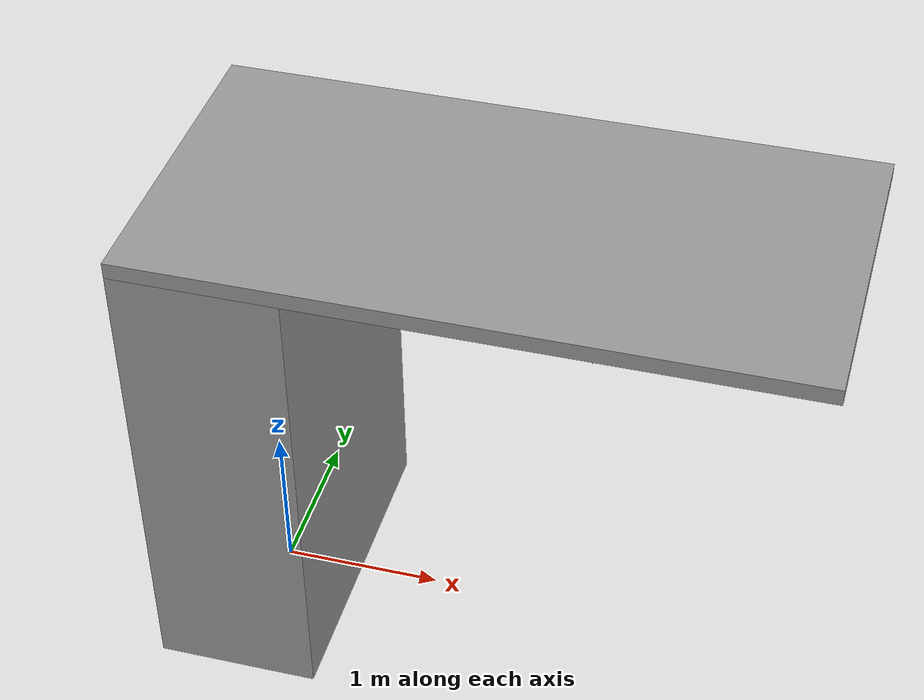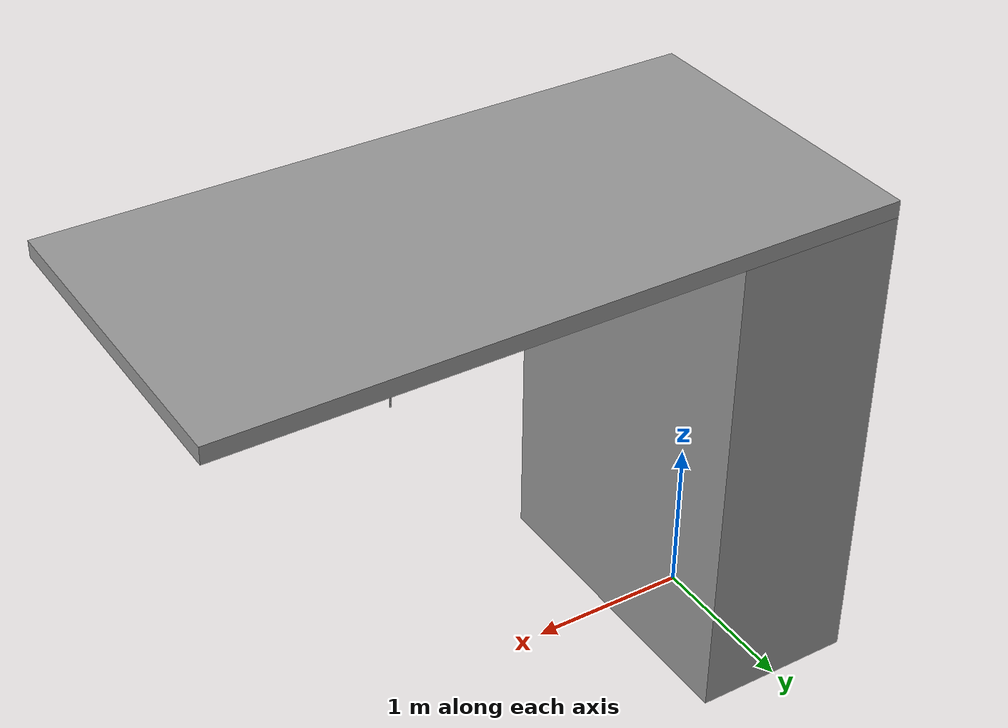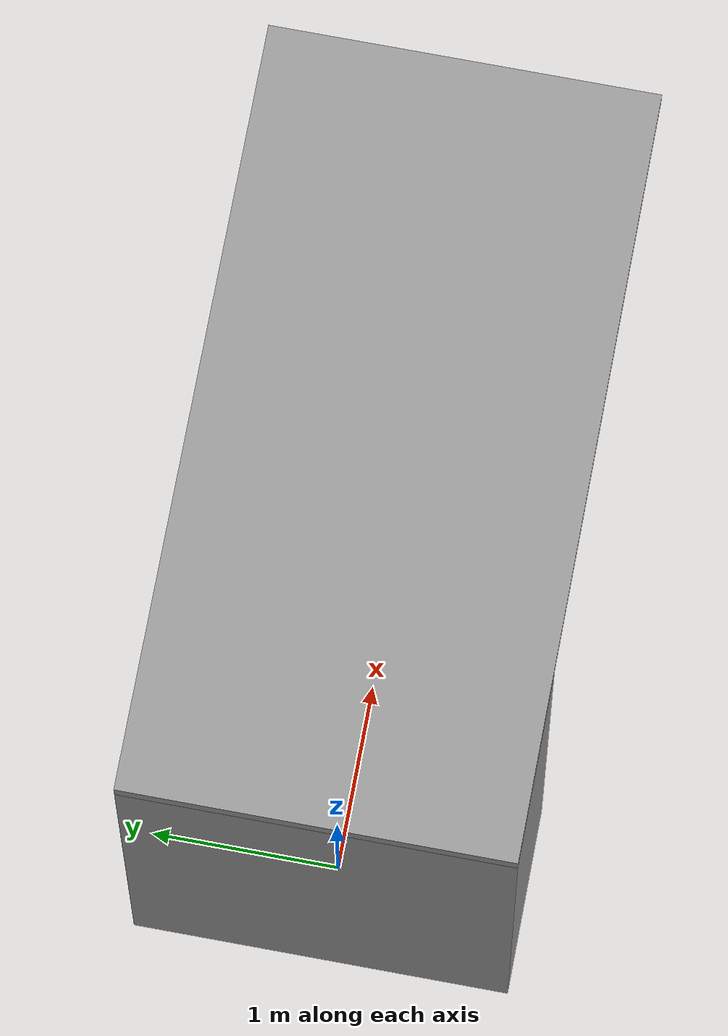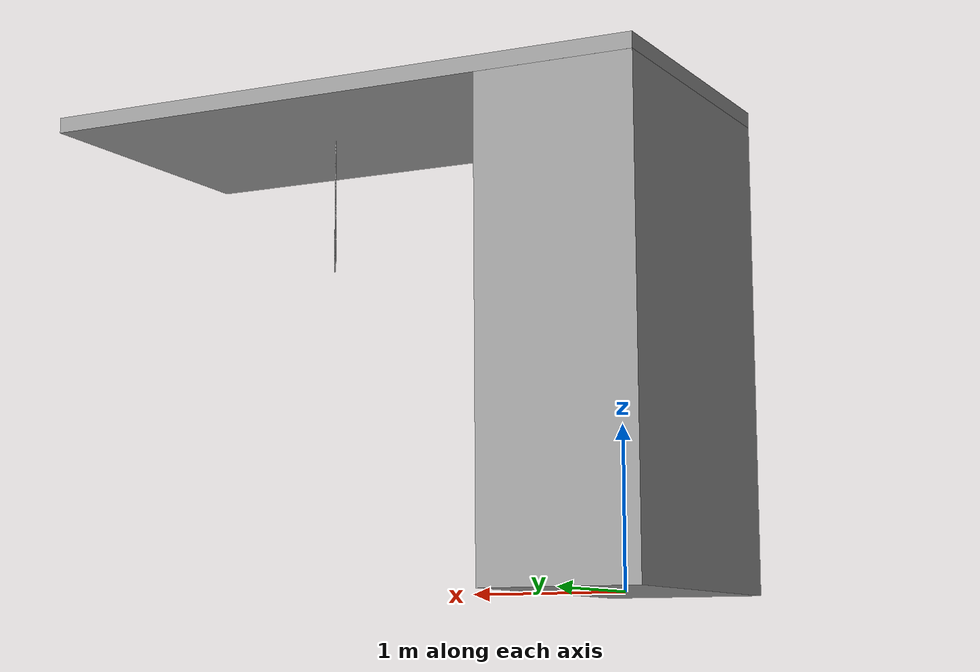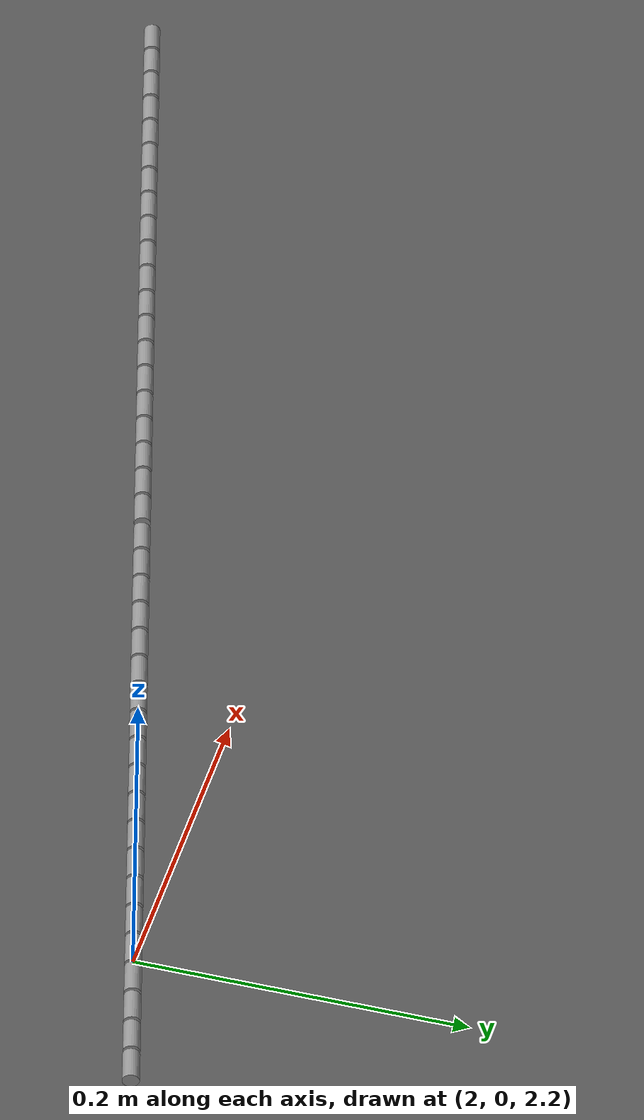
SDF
<?xml version="1.0" ?>
<sdf version="1.7">
  <model name="hang">
    <self_collide>true</self_collide>

     <include>
      <uri>model://hang_model</uri>
      <pose>0.0 0.0 1.5 0 0 0</pose>
    </include>

    <include>
      <uri>model://tether_test3</uri>
      <pose>2 0 2.12 0 0 0</pose>
    </include>

<joint name='JOINT_hang_tether' type='fixed'>
        <parent>tether_test3::link_33</parent>
        <child>hang_model::link_clone</child>
        <pose relative_to='tether_test3::link_33'> 0 0 0.011 0 -0 0</pose>
        <physics>
          <ode>
            <limit>
              <cfm>0</cfm>
              <erp>0.2</erp>
            </limit>
            <suspension>
              <cfm>0</cfm>
              <erp>0.2</erp>
            </suspension>
          </ode>
        </physics>
      </joint>

  </model>
</sdf>

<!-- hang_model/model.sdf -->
<sdf version='1.7'>
  <model name='hang_model'>
    <link name='link'>
      <inertial>
        <mass>220</mass>
        <inertia>
          <ixx>238.333</ixx>
          <ixy>0</ixy>
          <ixz>0</ixz>
          <iyy>183.333</iyy>
          <iyz>0</iyz>
          <izz>91.6667</izz>
        </inertia>
        <pose>0 0 0 0 -0.03 0</pose>
      </inertial>
      <self_collide>0</self_collide>
      <enable_wind>0</enable_wind>
      <kinematic>0</kinematic>
      <pose>0 0 0 0 -0 0</pose>
      <gravity>1</gravity>
      <visual name='visual'>
        <geometry>
          <box>
            <size>1 2 3</size>
          </box>
        </geometry>
        <material>
          <script>
            <name>Gazebo/Grey</name>
            <uri>file://media/materials/scripts/gazebo.material</uri>
          </script>
          <shader type='pixel'>
            <normal_map>__default__</normal_map>
          </shader>
          <ambient>0.3 0.3 0.3 1</ambient>
          <diffuse>0.7 0.7 0.7 1</diffuse>
          <specular>0.01 0.01 0.01 1</specular>
          <emissive>0 0 0 1</emissive>
        </material>
        <pose>0 0 0 0 -0 0</pose>
        <transparency>0</transparency>
        <cast_shadows>1</cast_shadows>
      </visual>
      <collision name='collision'>
        <laser_retro>0</laser_retro>
        <max_contacts>10</max_contacts>
        <pose>0 0 0 0 -0 0</pose>
        <geometry>
          <box>
            <size>1 2 3</size>
          </box>
        </geometry>
        <surface>
          <friction>
            <ode>
              <mu>1</mu>
              <mu2>1</mu2>
              <fdir1>0 0 0</fdir1>
              <slip1>0</slip1>
              <slip2>0</slip2>
            </ode>
            <torsional>
              <coefficient>1</coefficient>
              <patch_radius>0</patch_radius>
              <surface_radius>0</surface_radius>
              <use_patch_radius>1</use_patch_radius>
              <ode>
                <slip>0</slip>
              </ode>
            </torsional>
          </friction>
          <bounce>
            <restitution_coefficient>0</restitution_coefficient>
            <threshold>1e+06</threshold>
          </bounce>
          <contact>
            <collide_without_contact>0</collide_without_contact>
            <collide_without_contact_bitmask>1</collide_without_contact_bitmask>
            <collide_bitmask>1</collide_bitmask>
            <ode>
              <soft_cfm>0</soft_cfm>
              <soft_erp>0.2</soft_erp>
              <kp>1e+13</kp>
              <kd>1</kd>
              <max_vel>0.01</max_vel>
              <min_depth>0</min_depth>
            </ode>
            <bullet>
              <split_impulse>1</split_impulse>
              <split_impulse_penetration_threshold>-0.01</split_impulse_penetration_threshold>
              <soft_cfm>0</soft_cfm>
              <soft_erp>0.2</soft_erp>
              <kp>1e+13</kp>
              <kd>1</kd>
            </bullet>
          </contact>
        </surface>
      </collision>
    </link>
    <link name='link_clone'>
      <inertial>
        <mass>10</mass>
        <inertia>
          <ixx>3.34167</ixx>
          <ixy>0</ixy>
          <ixz>0</ixz>
          <iyy>13.3417</iyy>
          <iyz>0</iyz>
          <izz>16.6667</izz>
        </inertia>
        <pose>0 0 0 0 -0 0</pose>
      </inertial>
      <self_collide>0</self_collide>
      <enable_wind>0</enable_wind>
      <kinematic>0</kinematic>
      <pose>1.5 -0 1.55 0 -0 -0.000177</pose>
      <gravity>1</gravity>
      <visual name='visual'>
        <geometry>
          <box>
            <size>4 2 0.1</size>
          </box>
        </geometry>
        <material>
          <script>
            <name>Gazebo/Grey</name>
            <uri>file://media/materials/scripts/gazebo.material</uri>
          </script>
          <shader type='pixel'>
            <normal_map>__default__</normal_map>
          </shader>
          <ambient>0.3 0.3 0.3 1</ambient>
          <diffuse>0.7 0.7 0.7 1</diffuse>
          <specular>0.01 0.01 0.01 1</specular>
          <emissive>0 0 0 1</emissive>
        </material>
        <pose>0 0 0 0 -0 0</pose>
        <transparency>0</transparency>
        <cast_shadows>1</cast_shadows>
      </visual>
      <collision name='collision'>
        <laser_retro>0</laser_retro>
        <max_contacts>10</max_contacts>
        <pose>0 0 0 0 -0 0</pose>
        <geometry>
          <box>
            <size>4 2 0.1</size>
          </box>
        </geometry>
        <surface>
          <friction>
            <ode>
              <mu>1</mu>
              <mu2>1</mu2>
              <fdir1>0 0 0</fdir1>
              <slip1>0</slip1>
              <slip2>0</slip2>
            </ode>
            <torsional>
              <coefficient>1</coefficient>
              <patch_radius>0</patch_radius>
              <surface_radius>0</surface_radius>
              <use_patch_radius>1</use_patch_radius>
              <ode>
                <slip>0</slip>
              </ode>
            </torsional>
          </friction>
          <bounce>
            <restitution_coefficient>0</restitution_coefficient>
            <threshold>1e+06</threshold>
          </bounce>
          <contact>
            <collide_without_contact>0</collide_without_contact>
            <collide_without_contact_bitmask>1</collide_without_contact_bitmask>
            <collide_bitmask>1</collide_bitmask>
            <ode>
              <soft_cfm>0</soft_cfm>
              <soft_erp>0.2</soft_erp>
              <kp>1e+13</kp>
              <kd>1</kd>
              <max_vel>0.01</max_vel>
              <min_depth>0</min_depth>
            </ode>
            <bullet>
              <split_impulse>1</split_impulse>
              <split_impulse_penetration_threshold>-0.01</split_impulse_penetration_threshold>
              <soft_cfm>0</soft_cfm>
              <soft_erp>0.2</soft_erp>
              <kp>1e+13</kp>
              <kd>1</kd>
            </bullet>
          </contact>
        </surface>
      </collision>
    </link>
    <joint name='link_JOINT_0' type='fixed'>
      <parent>link</parent>
      <child>link_clone</child>
      <pose>-1.5 0 0 0 -0 0</pose>
      <physics>
        <ode>
          <limit>
            <cfm>0</cfm>
            <erp>0.2</erp>
          </limit>
          <suspension>
            <cfm>0</cfm>
            <erp>0.2</erp>
          </suspension>
        </ode>
      </physics>
    </joint>
    <static>0</static>
    <allow_auto_disable>1</allow_auto_disable>
  </model>
</sdf>

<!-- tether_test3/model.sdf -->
<sdf version='1.7'>
  <model name='tether_test3'>
    <link name='link_1'>
      <inertial>
        <mass>0.005</mass>
        <inertia>
          <ixx>7e-08</ixx>
          <ixy>0</ixy>
          <ixz>0</ixz>
          <iyy>7e-08</iyy>
          <iyz>0</iyz>
          <izz>6e-08</izz>
        </inertia>
        <pose>0 0 0 0 -0 0</pose>
      </inertial>
      <pose>0 0 0 0 -0 0</pose>
      <gravity>1</gravity>
      <self_collide>1</self_collide>
      <kinematic>0</kinematic>
      <enable_wind>0</enable_wind>
      <visual name='visual'>
        <pose>0 0 0 0 -0 0</pose>
        <geometry>
          <cylinder>
            <radius>0.005</radius>
            <length>0.02</length>
          </cylinder>
        </geometry>
        <material>
          <lighting>1</lighting>
          <script>
            <uri>file://media/materials/scripts/gazebo.material</uri>
            <name>Gazebo/Grey</name>
          </script>
          <shader type='pixel'>
            <normal_map>__default__</normal_map>
          </shader>
          <ambient>0.3 0.3 0.3 1</ambient>
          <diffuse>0.7 0.7 0.7 1</diffuse>
          <specular>0.01 0.01 0.01 1</specular>
          <emissive>0 0 0 1</emissive>
        </material>
        <transparency>0</transparency>
        <cast_shadows>1</cast_shadows>
      </visual>
      <collision name='collision'>
        <laser_retro>0</laser_retro>
        <max_contacts>10</max_contacts>
        <pose>0 0 0 0 -0 0</pose>
        <geometry>
          <cylinder>
            <radius>0.005</radius>
            <length>0.01</length>
          </cylinder>
        </geometry>
        <surface>
          <friction>
            <ode>
              <mu>1</mu>
              <mu2>1</mu2>
              <fdir1>0 0 0</fdir1>
              <slip1>0</slip1>
              <slip2>0</slip2>
            </ode>
            <torsional>
              <coefficient>1</coefficient>
              <patch_radius>0</patch_radius>
              <surface_radius>0</surface_radius>
              <use_patch_radius>1</use_patch_radius>
              <ode>
                <slip>0</slip>
              </ode>
            </torsional>
          </friction>
          <bounce>
            <restitution_coefficient>0</restitution_coefficient>
            <threshold>1e+06</threshold>
          </bounce>
          <contact>
            <collide_without_contact>0</collide_without_contact>
            <collide_without_contact_bitmask>1</collide_without_contact_bitmask>
            <collide_bitmask>1</collide_bitmask>
            <ode>
              <soft_cfm>0</soft_cfm>
              <soft_erp>0.2</soft_erp>
              <kp>1e+13</kp>
              <kd>1</kd>
              <max_vel>0.01</max_vel>
              <min_depth>0</min_depth>
            </ode>
            <bullet>
              <split_impulse>1</split_impulse>
              <split_impulse_penetration_threshold>-0.01</split_impulse_penetration_threshold>
              <soft_cfm>0</soft_cfm>
              <soft_erp>0.2</soft_erp>
              <kp>1e+13</kp>
              <kd>1</kd>
            </bullet>
          </contact>
        </surface>
      </collision>
    </link>
    <link name='link_0_clone_clone_7'>
      <inertial>
        <mass>0.005</mass>
        <inertia>
          <ixx>7e-08</ixx>
          <ixy>0</ixy>
          <ixz>0</ixz>
          <iyy>7e-08</iyy>
          <iyz>0</iyz>
          <izz>6e-08</izz>
        </inertia>
        <pose>0 0 0 0 -0 0</pose>
      </inertial>
      <pose>0 0 0.264 0 -0 0</pose>
      <gravity>1</gravity>
      <self_collide>1</self_collide>
      <kinematic>0</kinematic>
      <enable_wind>0</enable_wind>
      <visual name='visual'>
        <pose>0 0 0 0 -0 0</pose>
        <geometry>
          <cylinder>
            <radius>0.005</radius>
            <length>0.02</length>
          </cylinder>
        </geometry>
        <material>
          <lighting>1</lighting>
          <script>
            <uri>file://media/materials/scripts/gazebo.material</uri>
            <name>Gazebo/Grey</name>
          </script>
          <shader type='pixel'>
            <normal_map>__default__</normal_map>
          </shader>
          <ambient>0.3 0.3 0.3 1</ambient>
          <diffuse>0.7 0.7 0.7 1</diffuse>
          <specular>0.01 0.01 0.01 1</specular>
          <emissive>0 0 0 1</emissive>
        </material>
        <transparency>0</transparency>
        <cast_shadows>1</cast_shadows>
      </visual>
      <collision name='collision'>
        <laser_retro>0</laser_retro>
        <max_contacts>10</max_contacts>
        <pose>0 0 0 0 -0 0</pose>
        <geometry>
          <cylinder>
            <radius>0.005</radius>
            <length>0.01</length>
          </cylinder>
        </geometry>
        <surface>
          <friction>
            <ode>
              <mu>1</mu>
              <mu2>1</mu2>
              <fdir1>0 0 0</fdir1>
              <slip1>0</slip1>
              <slip2>0</slip2>
            </ode>
            <torsional>
              <coefficient>1</coefficient>
              <patch_radius>0</patch_radius>
              <surface_radius>0</surface_radius>
              <use_patch_radius>1</use_patch_radius>
              <ode>
                <slip>0</slip>
              </ode>
            </torsional>
          </friction>
          <bounce>
            <restitution_coefficient>0</restitution_coefficient>
            <threshold>1e+06</threshold>
          </bounce>
          <contact>
            <collide_without_contact>0</collide_without_contact>
            <collide_without_contact_bitmask>1</collide_without_contact_bitmask>
            <collide_bitmask>1</collide_bitmask>
            <ode>
              <soft_cfm>0</soft_cfm>
              <soft_erp>0.2</soft_erp>
              <kp>1e+13</kp>
              <kd>1</kd>
              <max_vel>0.01</max_vel>
              <min_depth>0</min_depth>
            </ode>
            <bullet>
              <split_impulse>1</split_impulse>
              <split_impulse_penetration_threshold>-0.01</split_impulse_penetration_threshold>
              <soft_cfm>0</soft_cfm>
              <soft_erp>0.2</soft_erp>
              <kp>1e+13</kp>
              <kd>1</kd>
            </bullet>
          </contact>
        </surface>
      </collision>
    </link>
    <link name='link_10'>
      <inertial>
        <mass>0.005</mass>
        <inertia>
          <ixx>7e-08</ixx>
          <ixy>0</ixy>
          <ixz>0</ixz>
          <iyy>7e-08</iyy>
          <iyz>0</iyz>
          <izz>6e-08</izz>
        </inertia>
        <pose>0 0 0 0 -0 0</pose>
      </inertial>
      <pose>0 0 0.154 0 -0 0</pose>
      <gravity>1</gravity>
      <self_collide>1</self_collide>
      <kinematic>0</kinematic>
      <enable_wind>0</enable_wind>
      <visual name='visual'>
        <pose>0 0 0 0 -0 0</pose>
        <geometry>
          <cylinder>
            <radius>0.005</radius>
            <length>0.02</length>
          </cylinder>
        </geometry>
        <material>
          <lighting>1</lighting>
          <script>
            <uri>file://media/materials/scripts/gazebo.material</uri>
            <name>Gazebo/Grey</name>
          </script>
          <shader type='pixel'>
            <normal_map>__default__</normal_map>
          </shader>
          <ambient>0.3 0.3 0.3 1</ambient>
          <diffuse>0.7 0.7 0.7 1</diffuse>
          <specular>0.01 0.01 0.01 1</specular>
          <emissive>0 0 0 1</emissive>
        </material>
        <transparency>0</transparency>
        <cast_shadows>1</cast_shadows>
      </visual>
      <collision name='collision'>
        <laser_retro>0</laser_retro>
        <max_contacts>10</max_contacts>
        <pose>0 0 0 0 -0 0</pose>
        <geometry>
          <cylinder>
            <radius>0.005</radius>
            <length>0.01</length>
          </cylinder>
        </geometry>
        <surface>
          <friction>
            <ode>
              <mu>1</mu>
              <mu2>1</mu2>
              <fdir1>0 0 0</fdir1>
              <slip1>0</slip1>
              <slip2>0</slip2>
            </ode>
            <torsional>
              <coefficient>1</coefficient>
              <patch_radius>0</patch_radius>
              <surface_radius>0</surface_radius>
              <use_patch_radius>1</use_patch_radius>
              <ode>
                <slip>0</slip>
              </ode>
            </torsional>
          </friction>
          <bounce>
            <restitution_coefficient>0</restitution_coefficient>
            <threshold>1e+06</threshold>
          </bounce>
          <contact>
            <collide_without_contact>0</collide_without_contact>
            <collide_without_contact_bitmask>1</collide_without_contact_bitmask>
            <collide_bitmask>1</collide_bitmask>
            <ode>
              <soft_cfm>0</soft_cfm>
              <soft_erp>0.2</soft_erp>
              <kp>1e+13</kp>
              <kd>1</kd>
              <max_vel>0.01</max_vel>
              <min_depth>0</min_depth>
            </ode>
            <bullet>
              <split_impulse>1</split_impulse>
              <split_impulse_penetration_threshold>-0.01</split_impulse_penetration_threshold>
              <soft_cfm>0</soft_cfm>
              <soft_erp>0.2</soft_erp>
              <kp>1e+13</kp>
              <kd>1</kd>
            </bullet>
          </contact>
        </surface>
      </collision>
    </link>
    <link name='link_11'>
      <inertial>
        <mass>0.005</mass>
        <inertia>
          <ixx>7e-08</ixx>
          <ixy>0</ixy>
          <ixz>0</ixz>
          <iyy>7e-08</iyy>
          <iyz>0</iyz>
          <izz>6e-08</izz>
        </inertia>
        <pose>0 0 0 0 -0 0</pose>
      </inertial>
      <pose>0 0 0.132 0 -0 0</pose>
      <gravity>1</gravity>
      <self_collide>1</self_collide>
      <kinematic>0</kinematic>
      <enable_wind>0</enable_wind>
      <visual name='visual'>
        <pose>0 0 0 0 -0 0</pose>
        <geometry>
          <cylinder>
            <radius>0.005</radius>
            <length>0.02</length>
          </cylinder>
        </geometry>
        <material>
          <lighting>1</lighting>
          <script>
            <uri>file://media/materials/scripts/gazebo.material</uri>
            <name>Gazebo/Grey</name>
          </script>
          <shader type='pixel'>
            <normal_map>__default__</normal_map>
          </shader>
          <ambient>0.3 0.3 0.3 1</ambient>
          <diffuse>0.7 0.7 0.7 1</diffuse>
          <specular>0.01 0.01 0.01 1</specular>
          <emissive>0 0 0 1</emissive>
        </material>
        <transparency>0</transparency>
        <cast_shadows>1</cast_shadows>
      </visual>
      <collision name='collision'>
        <laser_retro>0</laser_retro>
        <max_contacts>10</max_contacts>
        <pose>0 0 0 0 -0 0</pose>
        <geometry>
          <cylinder>
            <radius>0.005</radius>
            <length>0.01</length>
          </cylinder>
        </geometry>
        <surface>
          <friction>
            <ode>
              <mu>1</mu>
              <mu2>1</mu2>
              <fdir1>0 0 0</fdir1>
              <slip1>0</slip1>
              <slip2>0</slip2>
            </ode>
            <torsional>
              <coefficient>1</coefficient>
              <patch_radius>0</patch_radius>
              <surface_radius>0</surface_radius>
              <use_patch_radius>1</use_patch_radius>
              <ode>
                <slip>0</slip>
              </ode>
            </torsional>
          </friction>
          <bounce>
            <restitution_coefficient>0</restitution_coefficient>
            <threshold>1e+06</threshold>
          </bounce>
          <contact>
            <collide_without_contact>0</collide_without_contact>
            <collide_without_contact_bitmask>1</collide_without_contact_bitmask>
            <collide_bitmask>1</collide_bitmask>
            <ode>
              <soft_cfm>0</soft_cfm>
              <soft_erp>0.2</soft_erp>
              <kp>1e+13</kp>
              <kd>1</kd>
              <max_vel>0.01</max_vel>
              <min_depth>0</min_depth>
            </ode>
            <bullet>
              <split_impulse>1</split_impulse>
              <split_impulse_penetration_threshold>-0.01</split_impulse_penetration_threshold>
              <soft_cfm>0</soft_cfm>
              <soft_erp>0.2</soft_erp>
              <kp>1e+13</kp>
              <kd>1</kd>
            </bullet>
          </contact>
        </surface>
      </collision>
    </link>
    <link name='link_12'>
      <inertial>
        <mass>0.005</mass>
        <inertia>
          <ixx>7e-08</ixx>
          <ixy>0</ixy>
          <ixz>0</ixz>
          <iyy>7e-08</iyy>
          <iyz>0</iyz>
          <izz>6e-08</izz>
        </inertia>
        <pose>0 0 0 0 -0 0</pose>
      </inertial>
      <pose>0 0 0.286 0 -0 0</pose>
      <gravity>1</gravity>
      <self_collide>1</self_collide>
      <kinematic>0</kinematic>
      <enable_wind>0</enable_wind>
      <visual name='visual'>
        <pose>0 0 0 0 -0 0</pose>
        <geometry>
          <cylinder>
            <radius>0.005</radius>
            <length>0.02</length>
          </cylinder>
        </geometry>
        <material>
          <lighting>1</lighting>
          <script>
            <uri>file://media/materials/scripts/gazebo.material</uri>
            <name>Gazebo/Grey</name>
          </script>
          <shader type='pixel'>
            <normal_map>__default__</normal_map>
          </shader>
          <ambient>0.3 0.3 0.3 1</ambient>
          <diffuse>0.7 0.7 0.7 1</diffuse>
          <specular>0.01 0.01 0.01 1</specular>
          <emissive>0 0 0 1</emissive>
        </material>
        <transparency>0</transparency>
        <cast_shadows>1</cast_shadows>
      </visual>
      <collision name='collision'>
        <laser_retro>0</laser_retro>
        <max_contacts>10</max_contacts>
        <pose>0 0 0 0 -0 0</pose>
        <geometry>
          <cylinder>
            <radius>0.005</radius>
            <length>0.01</length>
          </cylinder>
        </geometry>
        <surface>
          <friction>
            <ode>
              <mu>1</mu>
              <mu2>1</mu2>
              <fdir1>0 0 0</fdir1>
              <slip1>0</slip1>
              <slip2>0</slip2>
            </ode>
            <torsional>
              <coefficient>1</coefficient>
              <patch_radius>0</patch_radius>
              <surface_radius>0</surface_radius>
              <use_patch_radius>1</use_patch_radius>
              <ode>
                <slip>0</slip>
              </ode>
            </torsional>
          </friction>
          <bounce>
            <restitution_coefficient>0</restitution_coefficient>
            <threshold>1e+06</threshold>
          </bounce>
          <contact>
            <collide_without_contact>0</collide_without_contact>
            <collide_without_contact_bitmask>1</collide_without_contact_bitmask>
            <collide_bitmask>1</collide_bitmask>
            <ode>
              <soft_cfm>0</soft_cfm>
              <soft_erp>0.2</soft_erp>
              <kp>1e+13</kp>
              <kd>1</kd>
              <max_vel>0.01</max_vel>
              <min_depth>0</min_depth>
            </ode>
            <bullet>
              <split_impulse>1</split_impulse>
              <split_impulse_penetration_threshold>-0.01</split_impulse_penetration_threshold>
              <soft_cfm>0</soft_cfm>
              <soft_erp>0.2</soft_erp>
              <kp>1e+13</kp>
              <kd>1</kd>
            </bullet>
          </contact>
        </surface>
      </collision>
    </link>
    <link name='link_13'>
      <inertial>
        <mass>0.005</mass>
        <inertia>
          <ixx>7e-08</ixx>
          <ixy>0</ixy>
          <ixz>0</ixz>
          <iyy>7e-08</iyy>
          <iyz>0</iyz>
          <izz>6e-08</izz>
        </inertia>
        <pose>0 0 0 0 -0 0</pose>
      </inertial>
      <pose>0 0 0.308 0 -0 0</pose>
      <gravity>1</gravity>
      <self_collide>1</self_collide>
      <kinematic>0</kinematic>
      <enable_wind>0</enable_wind>
      <visual name='visual'>
        <pose>0 0 0 0 -0 0</pose>
        <geometry>
          <cylinder>
            <radius>0.005</radius>
            <length>0.02</length>
          </cylinder>
        </geometry>
        <material>
          <lighting>1</lighting>
          <script>
            <uri>file://media/materials/scripts/gazebo.material</uri>
            <name>Gazebo/Grey</name>
          </script>
          <shader type='pixel'>
            <normal_map>__default__</normal_map>
          </shader>
          <ambient>0.3 0.3 0.3 1</ambient>
          <diffuse>0.7 0.7 0.7 1</diffuse>
          <specular>0.01 0.01 0.01 1</specular>
          <emissive>0 0 0 1</emissive>
        </material>
        <transparency>0</transparency>
        <cast_shadows>1</cast_shadows>
      </visual>
      <collision name='collision'>
        <laser_retro>0</laser_retro>
        <max_contacts>10</max_contacts>
        <pose>0 0 0 0 -0 0</pose>
        <geometry>
          <cylinder>
            <radius>0.005</radius>
            <length>0.01</length>
          </cylinder>
        </geometry>
        <surface>
          <friction>
            <ode>
              <mu>1</mu>
              <mu2>1</mu2>
              <fdir1>0 0 0</fdir1>
              <slip1>0</slip1>
              <slip2>0</slip2>
            </ode>
            <torsional>
              <coefficient>1</coefficient>
              <patch_radius>0</patch_radius>
              <surface_radius>0</surface_radius>
              <use_patch_radius>1</use_patch_radius>
              <ode>
                <slip>0</slip>
              </ode>
            </torsional>
          </friction>
          <bounce>
            <restitution_coefficient>0</restitution_coefficient>
            <threshold>1e+06</threshold>
          </bounce>
          <contact>
            <collide_without_contact>0</collide_without_contact>
            <collide_without_contact_bitmask>1</collide_without_contact_bitmask>
            <collide_bitmask>1</collide_bitmask>
            <ode>
              <soft_cfm>0</soft_cfm>
              <soft_erp>0.2</soft_erp>
              <kp>1e+13</kp>
              <kd>1</kd>
              <max_vel>0.01</max_vel>
              <min_depth>0</min_depth>
            </ode>
            <bullet>
              <split_impulse>1</split_impulse>
              <split_impulse_penetration_threshold>-0.01</split_impulse_penetration_threshold>
              <soft_cfm>0</soft_cfm>
              <soft_erp>0.2</soft_erp>
              <kp>1e+13</kp>
              <kd>1</kd>
            </bullet>
          </contact>
        </surface>
      </collision>
    </link>
    <link name='link_14'>
      <inertial>
        <mass>0.005</mass>
        <inertia>
          <ixx>7e-08</ixx>
          <ixy>0</ixy>
          <ixz>0</ixz>
          <iyy>7e-08</iyy>
          <iyz>0</iyz>
          <izz>6e-08</izz>
        </inertia>
        <pose>0 0 0 0 -0 0</pose>
      </inertial>
      <pose>0 0 0.33 0 -0 0</pose>
      <gravity>1</gravity>
      <self_collide>1</self_collide>
      <kinematic>0</kinematic>
      <enable_wind>0</enable_wind>
      <visual name='visual'>
        <pose>0 0 0 0 -0 0</pose>
        <geometry>
          <cylinder>
            <radius>0.005</radius>
            <length>0.02</length>
          </cylinder>
        </geometry>
        <material>
          <lighting>1</lighting>
          <script>
            <uri>file://media/materials/scripts/gazebo.material</uri>
            <name>Gazebo/Grey</name>
          </script>
          <shader type='pixel'>
            <normal_map>__default__</normal_map>
          </shader>
          <ambient>0.3 0.3 0.3 1</ambient>
          <diffuse>0.7 0.7 0.7 1</diffuse>
          <specular>0.01 0.01 0.01 1</specular>
          <emissive>0 0 0 1</emissive>
        </material>
        <transparency>0</transparency>
        <cast_shadows>1</cast_shadows>
      </visual>
      <collision name='collision'>
        <laser_retro>0</laser_retro>
        <max_contacts>10</max_contacts>
        <pose>0 0 0 0 -0 0</pose>
        <geometry>
          <cylinder>
            <radius>0.005</radius>
            <length>0.01</length>
          </cylinder>
        </geometry>
        <surface>
          <friction>
            <ode>
              <mu>1</mu>
              <mu2>1</mu2>
              <fdir1>0 0 0</fdir1>
              <slip1>0</slip1>
              <slip2>0</slip2>
            </ode>
            <torsional>
              <coefficient>1</coefficient>
              <patch_radius>0</patch_radius>
              <surface_radius>0</surface_radius>
              <use_patch_radius>1</use_patch_radius>
              <ode>
                <slip>0</slip>
              </ode>
            </torsional>
          </friction>
          <bounce>
            <restitution_coefficient>0</restitution_coefficient>
            <threshold>1e+06</threshold>
          </bounce>
          <contact>
            <collide_without_contact>0</collide_without_contact>
            <collide_without_contact_bitmask>1</collide_without_contact_bitmask>
            <collide_bitmask>1</collide_bitmask>
            <ode>
              <soft_cfm>0</soft_cfm>
              <soft_erp>0.2</soft_erp>
              <kp>1e+13</kp>
              <kd>1</kd>
              <max_vel>0.01</max_vel>
              <min_depth>0</min_depth>
            </ode>
            <bullet>
              <split_impulse>1</split_impulse>
              <split_impulse_penetration_threshold>-0.01</split_impulse_penetration_threshold>
              <soft_cfm>0</soft_cfm>
              <soft_erp>0.2</soft_erp>
              <kp>1e+13</kp>
              <kd>1</kd>
            </bullet>
          </contact>
        </surface>
      </collision>
    </link>
    <link name='link_15'>
      <inertial>
        <mass>0.005</mass>
        <inertia>
          <ixx>7e-08</ixx>
          <ixy>0</ixy>
          <ixz>0</ixz>
          <iyy>7e-08</iyy>
          <iyz>0</iyz>
          <izz>6e-08</izz>
        </inertia>
        <pose>0 0 0 0 -0 0</pose>
      </inertial>
      <pose>0 0 0.352 0 -0 0</pose>
      <gravity>1</gravity>
      <self_collide>1</self_collide>
      <kinematic>0</kinematic>
      <enable_wind>0</enable_wind>
      <visual name='visual'>
        <pose>0 0 0 0 -0 0</pose>
        <geometry>
          <cylinder>
            <radius>0.005</radius>
            <length>0.02</length>
          </cylinder>
        </geometry>
        <material>
          <lighting>1</lighting>
          <script>
            <uri>file://media/materials/scripts/gazebo.material</uri>
            <name>Gazebo/Grey</name>
          </script>
          <shader type='pixel'>
            <normal_map>__default__</normal_map>
          </shader>
          <ambient>0.3 0.3 0.3 1</ambient>
          <diffuse>0.7 0.7 0.7 1</diffuse>
          <specular>0.01 0.01 0.01 1</specular>
          <emissive>0 0 0 1</emissive>
        </material>
        <transparency>0</transparency>
        <cast_shadows>1</cast_shadows>
      </visual>
      <collision name='collision'>
        <laser_retro>0</laser_retro>
        <max_contacts>10</max_contacts>
        <pose>0 0 0 0 -0 0</pose>
        <geometry>
          <cylinder>
            <radius>0.005</radius>
            <length>0.01</length>
          </cylinder>
        </geometry>
        <surface>
          <friction>
            <ode>
              <mu>1</mu>
              <mu2>1</mu2>
              <fdir1>0 0 0</fdir1>
              <slip1>0</slip1>
              <slip2>0</slip2>
            </ode>
            <torsional>
              <coefficient>1</coefficient>
              <patch_radius>0</patch_radius>
              <surface_radius>0</surface_radius>
              <use_patch_radius>1</use_patch_radius>
              <ode>
                <slip>0</slip>
              </ode>
            </torsional>
          </friction>
          <bounce>
            <restitution_coefficient>0</restitution_coefficient>
            <threshold>1e+06</threshold>
          </bounce>
          <contact>
            <collide_without_contact>0</collide_without_contact>
            <collide_without_contact_bitmask>1</collide_without_contact_bitmask>
            <collide_bitmask>1</collide_bitmask>
            <ode>
              <soft_cfm>0</soft_cfm>
              <soft_erp>0.2</soft_erp>
              <kp>1e+13</kp>
              <kd>1</kd>
              <max_vel>0.01</max_vel>
              <min_depth>0</min_depth>
            </ode>
            <bullet>
              <split_impulse>1</split_impulse>
              <split_impulse_penetration_threshold>-0.01</split_impulse_penetration_threshold>
              <soft_cfm>0</soft_cfm>
              <soft_erp>0.2</soft_erp>
              <kp>1e+13</kp>
              <kd>1</kd>
            </bullet>
          </contact>
        </surface>
      </collision>
    </link>
    <link name='link_16'>
      <inertial>
        <mass>0.005</mass>
        <inertia>
          <ixx>7e-08</ixx>
          <ixy>0</ixy>
          <ixz>0</ixz>
          <iyy>7e-08</iyy>
          <iyz>0</iyz>
          <izz>6e-08</izz>
        </inertia>
        <pose>0 0 0 0 -0 0</pose>
      </inertial>
      <pose>0 0 0.374 0 -0 0</pose>
      <gravity>1</gravity>
      <self_collide>1</self_collide>
      <kinematic>0</kinematic>
      <enable_wind>0</enable_wind>
      <visual name='visual'>
        <pose>0 0 0 0 -0 0</pose>
        <geometry>
          <cylinder>
            <radius>0.005</radius>
            <length>0.02</length>
          </cylinder>
        </geometry>
        <material>
          <lighting>1</lighting>
          <script>
            <uri>file://media/materials/scripts/gazebo.material</uri>
            <name>Gazebo/Grey</name>
          </script>
          <shader type='pixel'>
            <normal_map>__default__</normal_map>
          </shader>
          <ambient>0.3 0.3 0.3 1</ambient>
          <diffuse>0.7 0.7 0.7 1</diffuse>
          <specular>0.01 0.01 0.01 1</specular>
          <emissive>0 0 0 1</emissive>
        </material>
        <transparency>0</transparency>
        <cast_shadows>1</cast_shadows>
      </visual>
      <collision name='collision'>
        <laser_retro>0</laser_retro>
        <max_contacts>10</max_contacts>
        <pose>0 0 0 0 -0 0</pose>
        <geometry>
          <cylinder>
            <radius>0.005</radius>
            <length>0.01</length>
          </cylinder>
        </geometry>
        <surface>
          <friction>
            <ode>
              <mu>1</mu>
              <mu2>1</mu2>
              <fdir1>0 0 0</fdir1>
              <slip1>0</slip1>
              <slip2>0</slip2>
            </ode>
            <torsional>
              <coefficient>1</coefficient>
              <patch_radius>0</patch_radius>
              <surface_radius>0</surface_radius>
              <use_patch_radius>1</use_patch_radius>
              <ode>
                <slip>0</slip>
              </ode>
            </torsional>
          </friction>
          <bounce>
            <restitution_coefficient>0</restitution_coefficient>
            <threshold>1e+06</threshold>
          </bounce>
          <contact>
            <collide_without_contact>0</collide_without_contact>
            <collide_without_contact_bitmask>1</collide_without_contact_bitmask>
            <collide_bitmask>1</collide_bitmask>
            <ode>
              <soft_cfm>0</soft_cfm>
              <soft_erp>0.2</soft_erp>
              <kp>1e+13</kp>
              <kd>1</kd>
              <max_vel>0.01</max_vel>
              <min_depth>0</min_depth>
            </ode>
            <bullet>
              <split_impulse>1</split_impulse>
              <split_impulse_penetration_threshold>-0.01</split_impulse_penetration_threshold>
              <soft_cfm>0</soft_cfm>
              <soft_erp>0.2</soft_erp>
              <kp>1e+13</kp>
              <kd>1</kd>
            </bullet>
          </contact>
        </surface>
      </collision>
    </link>
    <link name='link_17'>
      <inertial>
        <mass>0.005</mass>
        <inertia>
          <ixx>7e-08</ixx>
          <ixy>0</ixy>
          <ixz>0</ixz>
          <iyy>7e-08</iyy>
          <iyz>0</iyz>
          <izz>6e-08</izz>
        </inertia>
        <pose>0 0 0 0 -0 0</pose>
      </inertial>
      <pose>0 0 0.552 0 -0 0</pose>
      <gravity>1</gravity>
      <self_collide>1</self_collide>
      <kinematic>0</kinematic>
      <enable_wind>0</enable_wind>
      <visual name='visual'>
        <pose>0 0 0 0 -0 0</pose>
        <geometry>
          <cylinder>
            <radius>0.005</radius>
            <length>0.02</length>
          </cylinder>
        </geometry>
        <material>
          <lighting>1</lighting>
          <script>
            <uri>file://media/materials/scripts/gazebo.material</uri>
            <name>Gazebo/Grey</name>
          </script>
          <shader type='pixel'>
            <normal_map>__default__</normal_map>
          </shader>
          <ambient>0.3 0.3 0.3 1</ambient>
          <diffuse>0.7 0.7 0.7 1</diffuse>
          <specular>0.01 0.01 0.01 1</specular>
          <emissive>0 0 0 1</emissive>
        </material>
        <transparency>0</transparency>
        <cast_shadows>1</cast_shadows>
      </visual>
      <collision name='collision'>
        <laser_retro>0</laser_retro>
        <max_contacts>10</max_contacts>
        <pose>0 0 0 0 -0 0</pose>
        <geometry>
          <cylinder>
            <radius>0.005</radius>
            <length>0.01</length>
          </cylinder>
        </geometry>
        <surface>
          <friction>
            <ode>
              <mu>1</mu>
              <mu2>1</mu2>
              <fdir1>0 0 0</fdir1>
              <slip1>0</slip1>
              <slip2>0</slip2>
            </ode>
            <torsional>
              <coefficient>1</coefficient>
              <patch_radius>0</patch_radius>
              <surface_radius>0</surface_radius>
              <use_patch_radius>1</use_patch_radius>
              <ode>
                <slip>0</slip>
              </ode>
            </torsional>
          </friction>
          <bounce>
            <restitution_coefficient>0</restitution_coefficient>
            <threshold>1e+06</threshold>
          </bounce>
          <contact>
            <collide_without_contact>0</collide_without_contact>
            <collide_without_contact_bitmask>1</collide_without_contact_bitmask>
            <collide_bitmask>1</collide_bitmask>
            <ode>
              <soft_cfm>0</soft_cfm>
              <soft_erp>0.2</soft_erp>
              <kp>1e+13</kp>
              <kd>1</kd>
              <max_vel>0.01</max_vel>
              <min_depth>0</min_depth>
            </ode>
            <bullet>
              <split_impulse>1</split_impulse>
              <split_impulse_penetration_threshold>-0.01</split_impulse_penetration_threshold>
              <soft_cfm>0</soft_cfm>
              <soft_erp>0.2</soft_erp>
              <kp>1e+13</kp>
              <kd>1</kd>
            </bullet>
          </contact>
        </surface>
      </collision>
    </link>
    <link name='link_18'>
      <inertial>
        <mass>0.005</mass>
        <inertia>
          <ixx>7e-08</ixx>
          <ixy>0</ixy>
          <ixz>0</ixz>
          <iyy>7e-08</iyy>
          <iyz>0</iyz>
          <izz>6e-08</izz>
        </inertia>
        <pose>0 0 0 0 -0 0</pose>
      </inertial>
      <pose>0 0 0.574 0 -0 0</pose>
      <gravity>1</gravity>
      <self_collide>1</self_collide>
      <kinematic>0</kinematic>
      <enable_wind>0</enable_wind>
      <visual name='visual'>
        <pose>0 0 0 0 -0 0</pose>
        <geometry>
          <cylinder>
            <radius>0.005</radius>
            <length>0.02</length>
          </cylinder>
        </geometry>
        <material>
          <lighting>1</lighting>
          <script>
            <uri>file://media/materials/scripts/gazebo.material</uri>
            <name>Gazebo/Grey</name>
          </script>
          <shader type='pixel'>
            <normal_map>__default__</normal_map>
          </shader>
          <ambient>0.3 0.3 0.3 1</ambient>
          <diffuse>0.7 0.7 0.7 1</diffuse>
          <specular>0.01 0.01 0.01 1</specular>
          <emissive>0 0 0 1</emissive>
        </material>
        <transparency>0</transparency>
        <cast_shadows>1</cast_shadows>
      </visual>
      <collision name='collision'>
        <laser_retro>0</laser_retro>
        <max_contacts>10</max_contacts>
        <pose>0 0 0 0 -0 0</pose>
        <geometry>
          <cylinder>
            <radius>0.005</radius>
            <length>0.01</length>
          </cylinder>
        </geometry>
        <surface>
          <friction>
            <ode>
              <mu>1</mu>
              <mu2>1</mu2>
              <fdir1>0 0 0</fdir1>
              <slip1>0</slip1>
              <slip2>0</slip2>
            </ode>
            <torsional>
              <coefficient>1</coefficient>
              <patch_radius>0</patch_radius>
              <surface_radius>0</surface_radius>
              <use_patch_radius>1</use_patch_radius>
              <ode>
                <slip>0</slip>
              </ode>
            </torsional>
          </friction>
          <bounce>
            <restitution_coefficient>0</restitution_coefficient>
            <threshold>1e+06</threshold>
          </bounce>
          <contact>
            <collide_without_contact>0</collide_without_contact>
            <collide_without_contact_bitmask>1</collide_without_contact_bitmask>
            <collide_bitmask>1</collide_bitmask>
            <ode>
              <soft_cfm>0</soft_cfm>
              <soft_erp>0.2</soft_erp>
              <kp>1e+13</kp>
              <kd>1</kd>
              <max_vel>0.01</max_vel>
              <min_depth>0</min_depth>
            </ode>
            <bullet>
              <split_impulse>1</split_impulse>
              <split_impulse_penetration_threshold>-0.01</split_impulse_penetration_threshold>
              <soft_cfm>0</soft_cfm>
              <soft_erp>0.2</soft_erp>
              <kp>1e+13</kp>
              <kd>1</kd>
            </bullet>
          </contact>
        </surface>
      </collision>
    </link>
    <link name='link_19'>
      <inertial>
        <mass>0.005</mass>
        <inertia>
          <ixx>7e-08</ixx>
          <ixy>0</ixy>
          <ixz>0</ixz>
          <iyy>7e-08</iyy>
          <iyz>0</iyz>
          <izz>6e-08</izz>
        </inertia>
        <pose>0 0 0 0 -0 0</pose>
      </inertial>
      <pose>0 0 0.596 0 -0 0</pose>
      <gravity>1</gravity>
      <self_collide>1</self_collide>
      <kinematic>0</kinematic>
      <enable_wind>0</enable_wind>
      <visual name='visual'>
        <pose>0 0 0 0 -0 0</pose>
        <geometry>
          <cylinder>
            <radius>0.005</radius>
            <length>0.02</length>
          </cylinder>
        </geometry>
        <material>
          <lighting>1</lighting>
          <script>
            <uri>file://media/materials/scripts/gazebo.material</uri>
            <name>Gazebo/Grey</name>
          </script>
          <shader type='pixel'>
            <normal_map>__default__</normal_map>
          </shader>
          <ambient>0.3 0.3 0.3 1</ambient>
          <diffuse>0.7 0.7 0.7 1</diffuse>
          <specular>0.01 0.01 0.01 1</specular>
          <emissive>0 0 0 1</emissive>
        </material>
        <transparency>0</transparency>
        <cast_shadows>1</cast_shadows>
      </visual>
      <collision name='collision'>
        <laser_retro>0</laser_retro>
        <max_contacts>10</max_contacts>
        <pose>0 0 0 0 -0 0</pose>
        <geometry>
          <cylinder>
            <radius>0.005</radius>
            <length>0.01</length>
          </cylinder>
        </geometry>
        <surface>
          <friction>
            <ode>
              <mu>1</mu>
              <mu2>1</mu2>
              <fdir1>0 0 0</fdir1>
              <slip1>0</slip1>
              <slip2>0</slip2>
            </ode>
            <torsional>
              <coefficient>1</coefficient>
              <patch_radius>0</patch_radius>
              <surface_radius>0</surface_radius>
              <use_patch_radius>1</use_patch_radius>
              <ode>
                <slip>0</slip>
              </ode>
            </torsional>
          </friction>
          <bounce>
            <restitution_coefficient>0</restitution_coefficient>
            <threshold>1e+06</threshold>
          </bounce>
          <contact>
            <collide_without_contact>0</collide_without_contact>
            <collide_without_contact_bitmask>1</collide_without_contact_bitmask>
            <collide_bitmask>1</collide_bitmask>
            <ode>
              <soft_cfm>0</soft_cfm>
              <soft_erp>0.2</soft_erp>
              <kp>1e+13</kp>
              <kd>1</kd>
              <max_vel>0.01</max_vel>
              <min_depth>0</min_depth>
            </ode>
            <bullet>
              <split_impulse>1</split_impulse>
              <split_impulse_penetration_threshold>-0.01</split_impulse_penetration_threshold>
              <soft_cfm>0</soft_cfm>
              <soft_erp>0.2</soft_erp>
              <kp>1e+13</kp>
              <kd>1</kd>
            </bullet>
          </contact>
        </surface>
      </collision>
    </link>
    <link name='link_2'>
      <inertial>
        <mass>0.005</mass>
        <inertia>
          <ixx>7e-08</ixx>
          <ixy>0</ixy>
          <ixz>0</ixz>
          <iyy>7e-08</iyy>
          <iyz>0</iyz>
          <izz>6e-08</izz>
        </inertia>
        <pose>0 0 0 0 -0 0</pose>
      </inertial>
      <pose>0 0 0.11 0 -0 0</pose>
      <gravity>1</gravity>
      <self_collide>1</self_collide>
      <kinematic>0</kinematic>
      <enable_wind>0</enable_wind>
      <visual name='visual'>
        <pose>0 0 0 0 -0 0</pose>
        <geometry>
          <cylinder>
            <radius>0.005</radius>
            <length>0.02</length>
          </cylinder>
        </geometry>
        <material>
          <lighting>1</lighting>
          <script>
            <uri>file://media/materials/scripts/gazebo.material</uri>
            <name>Gazebo/Grey</name>
          </script>
          <shader type='pixel'>
            <normal_map>__default__</normal_map>
          </shader>
          <ambient>0.3 0.3 0.3 1</ambient>
          <diffuse>0.7 0.7 0.7 1</diffuse>
          <specular>0.01 0.01 0.01 1</specular>
          <emissive>0 0 0 1</emissive>
        </material>
        <transparency>0</transparency>
        <cast_shadows>1</cast_shadows>
      </visual>
      <collision name='collision'>
        <laser_retro>0</laser_retro>
        <max_contacts>10</max_contacts>
        <pose>0 0 0 0 -0 0</pose>
        <geometry>
          <cylinder>
            <radius>0.005</radius>
            <length>0.01</length>
          </cylinder>
        </geometry>
        <surface>
          <friction>
            <ode>
              <mu>1</mu>
              <mu2>1</mu2>
              <fdir1>0 0 0</fdir1>
              <slip1>0</slip1>
              <slip2>0</slip2>
            </ode>
            <torsional>
              <coefficient>1</coefficient>
              <patch_radius>0</patch_radius>
              <surface_radius>0</surface_radius>
              <use_patch_radius>1</use_patch_radius>
              <ode>
                <slip>0</slip>
              </ode>
            </torsional>
          </friction>
          <bounce>
            <restitution_coefficient>0</restitution_coefficient>
            <threshold>1e+06</threshold>
          </bounce>
          <contact>
            <collide_without_contact>0</collide_without_contact>
            <collide_without_contact_bitmask>1</collide_without_contact_bitmask>
            <collide_bitmask>1</collide_bitmask>
            <ode>
              <soft_cfm>0</soft_cfm>
              <soft_erp>0.2</soft_erp>
              <kp>1e+13</kp>
              <kd>1</kd>
              <max_vel>0.01</max_vel>
              <min_depth>0</min_depth>
            </ode>
            <bullet>
              <split_impulse>1</split_impulse>
              <split_impulse_penetration_threshold>-0.01</split_impulse_penetration_threshold>
              <soft_cfm>0</soft_cfm>
              <soft_erp>0.2</soft_erp>
              <kp>1e+13</kp>
              <kd>1</kd>
            </bullet>
          </contact>
        </surface>
      </collision>
    </link>
    <link name='link_20'>
      <inertial>
        <mass>0.005</mass>
        <inertia>
          <ixx>7e-08</ixx>
          <ixy>0</ixy>
          <ixz>0</ixz>
          <iyy>7e-08</iyy>
          <iyz>0</iyz>
          <izz>6e-08</izz>
        </inertia>
        <pose>0 0 0 0 -0 0</pose>
      </inertial>
      <pose>0 0 0.618 0 -0 0</pose>
      <gravity>1</gravity>
      <self_collide>1</self_collide>
      <kinematic>0</kinematic>
      <enable_wind>0</enable_wind>
      <visual name='visual'>
        <pose>0 0 0 0 -0 0</pose>
        <geometry>
          <cylinder>
            <radius>0.005</radius>
            <length>0.02</length>
          </cylinder>
        </geometry>
        <material>
          <lighting>1</lighting>
          <script>
            <uri>file://media/materials/scripts/gazebo.material</uri>
            <name>Gazebo/Grey</name>
          </script>
          <shader type='pixel'>
            <normal_map>__default__</normal_map>
          </shader>
          <ambient>0.3 0.3 0.3 1</ambient>
          <diffuse>0.7 0.7 0.7 1</diffuse>
          <specular>0.01 0.01 0.01 1</specular>
          <emissive>0 0 0 1</emissive>
        </material>
        <transparency>0</transparency>
        <cast_shadows>1</cast_shadows>
      </visual>
      <collision name='collision'>
        <laser_retro>0</laser_retro>
        <max_contacts>10</max_contacts>
        <pose>0 0 0 0 -0 0</pose>
        <geometry>
          <cylinder>
            <radius>0.005</radius>
            <length>0.01</length>
          </cylinder>
        </geometry>
        <surface>
          <friction>
            <ode>
              <mu>1</mu>
              <mu2>1</mu2>
              <fdir1>0 0 0</fdir1>
              <slip1>0</slip1>
              <slip2>0</slip2>
            </ode>
            <torsional>
              <coefficient>1</coefficient>
              <patch_radius>0</patch_radius>
              <surface_radius>0</surface_radius>
              <use_patch_radius>1</use_patch_radius>
              <ode>
                <slip>0</slip>
              </ode>
            </torsional>
          </friction>
          <bounce>
            <restitution_coefficient>0</restitution_coefficient>
            <threshold>1e+06</threshold>
          </bounce>
          <contact>
            <collide_without_contact>0</collide_without_contact>
            <collide_without_contact_bitmask>1</collide_without_contact_bitmask>
            <collide_bitmask>1</collide_bitmask>
            <ode>
              <soft_cfm>0</soft_cfm>
              <soft_erp>0.2</soft_erp>
              <kp>1e+13</kp>
              <kd>1</kd>
              <max_vel>0.01</max_vel>
              <min_depth>0</min_depth>
            </ode>
            <bullet>
              <split_impulse>1</split_impulse>
              <split_impulse_penetration_threshold>-0.01</split_impulse_penetration_threshold>
              <soft_cfm>0</soft_cfm>
              <soft_erp>0.2</soft_erp>
              <kp>1e+13</kp>
              <kd>1</kd>
            </bullet>
          </contact>
        </surface>
      </collision>
    </link>
    <link name='link_21'>
      <inertial>
        <mass>0.005</mass>
        <inertia>
          <ixx>7e-08</ixx>
          <ixy>0</ixy>
          <ixz>0</ixz>
          <iyy>7e-08</iyy>
          <iyz>0</iyz>
          <izz>6e-08</izz>
        </inertia>
        <pose>0 0 0 0 -0 0</pose>
      </inertial>
      <pose>0 0 0.64 0 -0 0</pose>
      <gravity>1</gravity>
      <self_collide>1</self_collide>
      <kinematic>0</kinematic>
      <enable_wind>0</enable_wind>
      <visual name='visual'>
        <pose>0 0 0 0 -0 0</pose>
        <geometry>
          <cylinder>
            <radius>0.005</radius>
            <length>0.02</length>
          </cylinder>
        </geometry>
        <material>
          <lighting>1</lighting>
          <script>
            <uri>file://media/materials/scripts/gazebo.material</uri>
            <name>Gazebo/Grey</name>
          </script>
          <shader type='pixel'>
            <normal_map>__default__</normal_map>
          </shader>
          <ambient>0.3 0.3 0.3 1</ambient>
          <diffuse>0.7 0.7 0.7 1</diffuse>
          <specular>0.01 0.01 0.01 1</specular>
          <emissive>0 0 0 1</emissive>
        </material>
        <transparency>0</transparency>
        <cast_shadows>1</cast_shadows>
      </visual>
      <collision name='collision'>
        <laser_retro>0</laser_retro>
        <max_contacts>10</max_contacts>
        <pose>0 0 0 0 -0 0</pose>
        <geometry>
          <cylinder>
            <radius>0.005</radius>
            <length>0.01</length>
          </cylinder>
        </geometry>
        <surface>
          <friction>
            <ode>
              <mu>1</mu>
              <mu2>1</mu2>
              <fdir1>0 0 0</fdir1>
              <slip1>0</slip1>
              <slip2>0</slip2>
            </ode>
            <torsional>
              <coefficient>1</coefficient>
              <patch_radius>0</patch_radius>
              <surface_radius>0</surface_radius>
              <use_patch_radius>1</use_patch_radius>
              <ode>
                <slip>0</slip>
              </ode>
            </torsional>
          </friction>
          <bounce>
            <restitution_coefficient>0</restitution_coefficient>
            <threshold>1e+06</threshold>
          </bounce>
          <contact>
            <collide_without_contact>0</collide_without_contact>
            <collide_without_contact_bitmask>1</collide_without_contact_bitmask>
            <collide_bitmask>1</collide_bitmask>
            <ode>
              <soft_cfm>0</soft_cfm>
              <soft_erp>0.2</soft_erp>
              <kp>1e+13</kp>
              <kd>1</kd>
              <max_vel>0.01</max_vel>
              <min_depth>0</min_depth>
            </ode>
            <bullet>
              <split_impulse>1</split_impulse>
              <split_impulse_penetration_threshold>-0.01</split_impulse_penetration_threshold>
              <soft_cfm>0</soft_cfm>
              <soft_erp>0.2</soft_erp>
              <kp>1e+13</kp>
              <kd>1</kd>
            </bullet>
          </contact>
        </surface>
      </collision>
    </link>
    <link name='link_22'>
      <inertial>
        <mass>0.005</mass>
        <inertia>
          <ixx>7e-08</ixx>
          <ixy>0</ixy>
          <ixz>0</ixz>
          <iyy>7e-08</iyy>
          <iyz>0</iyz>
          <izz>6e-08</izz>
        </inertia>
        <pose>0 0 0 0 -0 0</pose>
      </inertial>
      <pose>0 0 0.662 0 -0 0</pose>
      <gravity>1</gravity>
      <self_collide>1</self_collide>
      <kinematic>0</kinematic>
      <enable_wind>0</enable_wind>
      <visual name='visual'>
        <pose>0 0 0 0 -0 0</pose>
        <geometry>
          <cylinder>
            <radius>0.005</radius>
            <length>0.02</length>
          </cylinder>
        </geometry>
        <material>
          <lighting>1</lighting>
          <script>
            <uri>file://media/materials/scripts/gazebo.material</uri>
            <name>Gazebo/Grey</name>
          </script>
          <shader type='pixel'>
            <normal_map>__default__</normal_map>
          </shader>
          <ambient>0.3 0.3 0.3 1</ambient>
          <diffuse>0.7 0.7 0.7 1</diffuse>
          <specular>0.01 0.01 0.01 1</specular>
          <emissive>0 0 0 1</emissive>
        </material>
        <transparency>0</transparency>
        <cast_shadows>1</cast_shadows>
      </visual>
      <collision name='collision'>
        <laser_retro>0</laser_retro>
        <max_contacts>10</max_contacts>
        <pose>0 0 0 0 -0 0</pose>
        <geometry>
          <cylinder>
            <radius>0.005</radius>
            <length>0.01</length>
          </cylinder>
        </geometry>
        <surface>
          <friction>
            <ode>
              <mu>1</mu>
              <mu2>1</mu2>
              <fdir1>0 0 0</fdir1>
              <slip1>0</slip1>
              <slip2>0</slip2>
            </ode>
            <torsional>
              <coefficient>1</coefficient>
              <patch_radius>0</patch_radius>
              <surface_radius>0</surface_radius>
              <use_patch_radius>1</use_patch_radius>
              <ode>
                <slip>0</slip>
              </ode>
            </torsional>
          </friction>
          <bounce>
            <restitution_coefficient>0</restitution_coefficient>
            <threshold>1e+06</threshold>
          </bounce>
          <contact>
            <collide_without_contact>0</collide_without_contact>
            <collide_without_contact_bitmask>1</collide_without_contact_bitmask>
            <collide_bitmask>1</collide_bitmask>
            <ode>
              <soft_cfm>0</soft_cfm>
              <soft_erp>0.2</soft_erp>
              <kp>1e+13</kp>
              <kd>1</kd>
              <max_vel>0.01</max_vel>
              <min_depth>0</min_depth>
            </ode>
            <bullet>
              <split_impulse>1</split_impulse>
              <split_impulse_penetration_threshold>-0.01</split_impulse_penetration_threshold>
              <soft_cfm>0</soft_cfm>
              <soft_erp>0.2</soft_erp>
              <kp>1e+13</kp>
              <kd>1</kd>
            </bullet>
          </contact>
        </surface>
      </collision>
    </link>
    <link name='link_23'>
      <inertial>
        <mass>0.005</mass>
        <inertia>
          <ixx>7e-08</ixx>
          <ixy>0</ixy>
          <ixz>0</ixz>
          <iyy>7e-08</iyy>
          <iyz>0</iyz>
          <izz>6e-08</izz>
        </inertia>
        <pose>0 0 0 0 -0 0</pose>
      </inertial>
      <pose>0 0 0.684 0 -0 0</pose>
      <gravity>1</gravity>
      <self_collide>1</self_collide>
      <kinematic>0</kinematic>
      <enable_wind>0</enable_wind>
      <visual name='visual'>
        <pose>0 0 0 0 -0 0</pose>
        <geometry>
          <cylinder>
            <radius>0.005</radius>
            <length>0.02</length>
          </cylinder>
        </geometry>
        <material>
          <lighting>1</lighting>
          <script>
            <uri>file://media/materials/scripts/gazebo.material</uri>
            <name>Gazebo/Grey</name>
          </script>
          <shader type='pixel'>
            <normal_map>__default__</normal_map>
          </shader>
          <ambient>0.3 0.3 0.3 1</ambient>
          <diffuse>0.7 0.7 0.7 1</diffuse>
          <specular>0.01 0.01 0.01 1</specular>
          <emissive>0 0 0 1</emissive>
        </material>
        <transparency>0</transparency>
        <cast_shadows>1</cast_shadows>
      </visual>
      <collision name='collision'>
        <laser_retro>0</laser_retro>
        <max_contacts>10</max_contacts>
        <pose>0 0 0 0 -0 0</pose>
        <geometry>
          <cylinder>
            <radius>0.005</radius>
            <length>0.01</length>
          </cylinder>
        </geometry>
        <surface>
          <friction>
            <ode>
              <mu>1</mu>
              <mu2>1</mu2>
              <fdir1>0 0 0</fdir1>
              <slip1>0</slip1>
              <slip2>0</slip2>
            </ode>
            <torsional>
              <coefficient>1</coefficient>
              <patch_radius>0</patch_radius>
              <surface_radius>0</surface_radius>
              <use_patch_radius>1</use_patch_radius>
              <ode>
                <slip>0</slip>
              </ode>
            </torsional>
          </friction>
          <bounce>
            <restitution_coefficient>0</restitution_coefficient>
            <threshold>1e+06</threshold>
          </bounce>
          <contact>
            <collide_without_contact>0</collide_without_contact>
            <collide_without_contact_bitmask>1</collide_without_contact_bitmask>
            <collide_bitmask>1</collide_bitmask>
            <ode>
              <soft_cfm>0</soft_cfm>
              <soft_erp>0.2</soft_erp>
              <kp>1e+13</kp>
              <kd>1</kd>
              <max_vel>0.01</max_vel>
              <min_depth>0</min_depth>
            </ode>
            <bullet>
              <split_impulse>1</split_impulse>
              <split_impulse_penetration_threshold>-0.01</split_impulse_penetration_threshold>
              <soft_cfm>0</soft_cfm>
              <soft_erp>0.2</soft_erp>
              <kp>1e+13</kp>
              <kd>1</kd>
            </bullet>
          </contact>
        </surface>
      </collision>
    </link>
    <link name='link_24'>
      <inertial>
        <mass>0.005</mass>
        <inertia>
          <ixx>7e-08</ixx>
          <ixy>0</ixy>
          <ixz>0</ixz>
          <iyy>7e-08</iyy>
          <iyz>0</iyz>
          <izz>6e-08</izz>
        </inertia>
        <pose>0 0 0 0 -0 0</pose>
      </inertial>
      <pose>0 0 0.706 0 -0 0</pose>
      <gravity>1</gravity>
      <self_collide>1</self_collide>
      <kinematic>0</kinematic>
      <enable_wind>0</enable_wind>
      <visual name='visual'>
        <pose>0 0 0 0 -0 0</pose>
        <geometry>
          <cylinder>
            <radius>0.005</radius>
            <length>0.02</length>
          </cylinder>
        </geometry>
        <material>
          <lighting>1</lighting>
          <script>
            <uri>file://media/materials/scripts/gazebo.material</uri>
            <name>Gazebo/Grey</name>
          </script>
          <shader type='pixel'>
            <normal_map>__default__</normal_map>
          </shader>
          <ambient>0.3 0.3 0.3 1</ambient>
          <diffuse>0.7 0.7 0.7 1</diffuse>
          <specular>0.01 0.01 0.01 1</specular>
          <emissive>0 0 0 1</emissive>
        </material>
        <transparency>0</transparency>
        <cast_shadows>1</cast_shadows>
      </visual>
      <collision name='collision'>
        <laser_retro>0</laser_retro>
        <max_contacts>10</max_contacts>
        <pose>0 0 0 0 -0 0</pose>
        <geometry>
          <cylinder>
            <radius>0.005</radius>
            <length>0.01</length>
          </cylinder>
        </geometry>
        <surface>
          <friction>
            <ode>
              <mu>1</mu>
              <mu2>1</mu2>
              <fdir1>0 0 0</fdir1>
              <slip1>0</slip1>
              <slip2>0</slip2>
            </ode>
            <torsional>
              <coefficient>1</coefficient>
              <patch_radius>0</patch_radius>
              <surface_radius>0</surface_radius>
              <use_patch_radius>1</use_patch_radius>
              <ode>
                <slip>0</slip>
              </ode>
            </torsional>
          </friction>
          <bounce>
            <restitution_coefficient>0</restitution_coefficient>
            <threshold>1e+06</threshold>
          </bounce>
          <contact>
            <collide_without_contact>0</collide_without_contact>
            <collide_without_contact_bitmask>1</collide_without_contact_bitmask>
            <collide_bitmask>1</collide_bitmask>
            <ode>
              <soft_cfm>0</soft_cfm>
              <soft_erp>0.2</soft_erp>
              <kp>1e+13</kp>
              <kd>1</kd>
              <max_vel>0.01</max_vel>
              <min_depth>0</min_depth>
            </ode>
            <bullet>
              <split_impulse>1</split_impulse>
              <split_impulse_penetration_threshold>-0.01</split_impulse_penetration_threshold>
              <soft_cfm>0</soft_cfm>
              <soft_erp>0.2</soft_erp>
              <kp>1e+13</kp>
              <kd>1</kd>
            </bullet>
          </contact>
        </surface>
      </collision>
    </link>
    <link name='link_25'>
      <inertial>
        <mass>0.005</mass>
        <inertia>
          <ixx>7e-08</ixx>
          <ixy>0</ixy>
          <ixz>0</ixz>
          <iyy>7e-08</iyy>
          <iyz>0</iyz>
          <izz>6e-08</izz>
        </inertia>
        <pose>0 0 0 0 -0 0</pose>
      </inertial>
      <pose>0 0 0.728 0 -0 0</pose>
      <gravity>1</gravity>
      <self_collide>1</self_collide>
      <kinematic>0</kinematic>
      <enable_wind>0</enable_wind>
      <visual name='visual'>
        <pose>0 0 0 0 -0 0</pose>
        <geometry>
          <cylinder>
            <radius>0.005</radius>
            <length>0.02</length>
          </cylinder>
        </geometry>
        <material>
          <lighting>1</lighting>
          <script>
            <uri>file://media/materials/scripts/gazebo.material</uri>
            <name>Gazebo/Grey</name>
          </script>
          <shader type='pixel'>
            <normal_map>__default__</normal_map>
          </shader>
          <ambient>0.3 0.3 0.3 1</ambient>
          <diffuse>0.7 0.7 0.7 1</diffuse>
          <specular>0.01 0.01 0.01 1</specular>
          <emissive>0 0 0 1</emissive>
        </material>
        <transparency>0</transparency>
        <cast_shadows>1</cast_shadows>
      </visual>
      <collision name='collision'>
        <laser_retro>0</laser_retro>
        <max_contacts>10</max_contacts>
        <pose>0 0 0 0 -0 0</pose>
        <geometry>
          <cylinder>
            <radius>0.005</radius>
            <length>0.01</length>
          </cylinder>
        </geometry>
        <surface>
          <friction>
            <ode>
              <mu>1</mu>
              <mu2>1</mu2>
              <fdir1>0 0 0</fdir1>
              <slip1>0</slip1>
              <slip2>0</slip2>
            </ode>
            <torsional>
              <coefficient>1</coefficient>
              <patch_radius>0</patch_radius>
              <surface_radius>0</surface_radius>
              <use_patch_radius>1</use_patch_radius>
              <ode>
                <slip>0</slip>
              </ode>
            </torsional>
          </friction>
          <bounce>
            <restitution_coefficient>0</restitution_coefficient>
            <threshold>1e+06</threshold>
          </bounce>
          <contact>
            <collide_without_contact>0</collide_without_contact>
            <collide_without_contact_bitmask>1</collide_without_contact_bitmask>
            <collide_bitmask>1</collide_bitmask>
            <ode>
              <soft_cfm>0</soft_cfm>
              <soft_erp>0.2</soft_erp>
              <kp>1e+13</kp>
              <kd>1</kd>
              <max_vel>0.01</max_vel>
              <min_depth>0</min_depth>
            </ode>
            <bullet>
              <split_impulse>1</split_impulse>
              <split_impulse_penetration_threshold>-0.01</split_impulse_penetration_threshold>
              <soft_cfm>0</soft_cfm>
              <soft_erp>0.2</soft_erp>
              <kp>1e+13</kp>
              <kd>1</kd>
            </bullet>
          </contact>
        </surface>
      </collision>
    </link>
    <link name='link_26'>
      <inertial>
        <mass>0.005</mass>
        <inertia>
          <ixx>7e-08</ixx>
          <ixy>0</ixy>
          <ixz>0</ixz>
          <iyy>7e-08</iyy>
          <iyz>0</iyz>
          <izz>6e-08</izz>
        </inertia>
        <pose>0 0 0 0 -0 0</pose>
      </inertial>
      <pose>0 0 0.75 0 -0 0</pose>
      <gravity>1</gravity>
      <self_collide>1</self_collide>
      <kinematic>0</kinematic>
      <enable_wind>0</enable_wind>
      <visual name='visual'>
        <pose>0 0 0 0 -0 0</pose>
        <geometry>
          <cylinder>
            <radius>0.005</radius>
            <length>0.02</length>
          </cylinder>
        </geometry>
        <material>
          <lighting>1</lighting>
          <script>
            <uri>file://media/materials/scripts/gazebo.material</uri>
            <name>Gazebo/Grey</name>
          </script>
          <shader type='pixel'>
            <normal_map>__default__</normal_map>
          </shader>
          <ambient>0.3 0.3 0.3 1</ambient>
          <diffuse>0.7 0.7 0.7 1</diffuse>
          <specular>0.01 0.01 0.01 1</specular>
          <emissive>0 0 0 1</emissive>
        </material>
        <transparency>0</transparency>
        <cast_shadows>1</cast_shadows>
      </visual>
      <collision name='collision'>
        <laser_retro>0</laser_retro>
        <max_contacts>10</max_contacts>
        <pose>0 0 0 0 -0 0</pose>
        <geometry>
          <cylinder>
            <radius>0.005</radius>
            <length>0.01</length>
          </cylinder>
        </geometry>
        <surface>
          <friction>
            <ode>
              <mu>1</mu>
              <mu2>1</mu2>
              <fdir1>0 0 0</fdir1>
              <slip1>0</slip1>
              <slip2>0</slip2>
            </ode>
            <torsional>
              <coefficient>1</coefficient>
              <patch_radius>0</patch_radius>
              <surface_radius>0</surface_radius>
              <use_patch_radius>1</use_patch_radius>
              <ode>
                <slip>0</slip>
              </ode>
            </torsional>
          </friction>
          <bounce>
            <restitution_coefficient>0</restitution_coefficient>
            <threshold>1e+06</threshold>
          </bounce>
          <contact>
            <collide_without_contact>0</collide_without_contact>
            <collide_without_contact_bitmask>1</collide_without_contact_bitmask>
            <collide_bitmask>1</collide_bitmask>
            <ode>
              <soft_cfm>0</soft_cfm>
              <soft_erp>0.2</soft_erp>
              <kp>1e+13</kp>
              <kd>1</kd>
              <max_vel>0.01</max_vel>
              <min_depth>0</min_depth>
            </ode>
            <bullet>
              <split_impulse>1</split_impulse>
              <split_impulse_penetration_threshold>-0.01</split_impulse_penetration_threshold>
              <soft_cfm>0</soft_cfm>
              <soft_erp>0.2</soft_erp>
              <kp>1e+13</kp>
              <kd>1</kd>
            </bullet>
          </contact>
        </surface>
      </collision>
    </link>
    <link name='link_27'>
      <inertial>
        <mass>0.005</mass>
        <inertia>
          <ixx>7e-08</ixx>
          <ixy>0</ixy>
          <ixz>0</ixz>
          <iyy>7e-08</iyy>
          <iyz>0</iyz>
          <izz>6e-08</izz>
        </inertia>
        <pose>0 0 0 0 -0 0</pose>
      </inertial>
      <pose>0 0 0.772 0 -0 0</pose>
      <gravity>1</gravity>
      <self_collide>1</self_collide>
      <kinematic>0</kinematic>
      <enable_wind>0</enable_wind>
      <visual name='visual'>
        <pose>0 0 0 0 -0 0</pose>
        <geometry>
          <cylinder>
            <radius>0.005</radius>
            <length>0.02</length>
          </cylinder>
        </geometry>
        <material>
          <lighting>1</lighting>
          <script>
            <uri>file://media/materials/scripts/gazebo.material</uri>
            <name>Gazebo/Grey</name>
          </script>
          <shader type='pixel'>
            <normal_map>__default__</normal_map>
          </shader>
          <ambient>0.3 0.3 0.3 1</ambient>
          <diffuse>0.7 0.7 0.7 1</diffuse>
          <specular>0.01 0.01 0.01 1</specular>
          <emissive>0 0 0 1</emissive>
        </material>
        <transparency>0</transparency>
        <cast_shadows>1</cast_shadows>
      </visual>
      <collision name='collision'>
        <laser_retro>0</laser_retro>
        <max_contacts>10</max_contacts>
        <pose>0 0 0 0 -0 0</pose>
        <geometry>
          <cylinder>
            <radius>0.005</radius>
            <length>0.01</length>
          </cylinder>
        </geometry>
        <surface>
          <friction>
            <ode>
              <mu>1</mu>
              <mu2>1</mu2>
              <fdir1>0 0 0</fdir1>
              <slip1>0</slip1>
              <slip2>0</slip2>
            </ode>
            <torsional>
              <coefficient>1</coefficient>
              <patch_radius>0</patch_radius>
              <surface_radius>0</surface_radius>
              <use_patch_radius>1</use_patch_radius>
              <ode>
                <slip>0</slip>
              </ode>
            </torsional>
          </friction>
          <bounce>
            <restitution_coefficient>0</restitution_coefficient>
            <threshold>1e+06</threshold>
          </bounce>
          <contact>
            <collide_without_contact>0</collide_without_contact>
            <collide_without_contact_bitmask>1</collide_without_contact_bitmask>
            <collide_bitmask>1</collide_bitmask>
            <ode>
              <soft_cfm>0</soft_cfm>
              <soft_erp>0.2</soft_erp>
              <kp>1e+13</kp>
              <kd>1</kd>
              <max_vel>0.01</max_vel>
              <min_depth>0</min_depth>
            </ode>
            <bullet>
              <split_impulse>1</split_impulse>
              <split_impulse_penetration_threshold>-0.01</split_impulse_penetration_threshold>
              <soft_cfm>0</soft_cfm>
              <soft_erp>0.2</soft_erp>
              <kp>1e+13</kp>
              <kd>1</kd>
            </bullet>
          </contact>
        </surface>
      </collision>
    </link>
    <link name='link_28'>
      <inertial>
        <mass>0.005</mass>
        <inertia>
          <ixx>7e-08</ixx>
          <ixy>0</ixy>
          <ixz>0</ixz>
          <iyy>7e-08</iyy>
          <iyz>0</iyz>
          <izz>6e-08</izz>
        </inertia>
        <pose>0 0 0 0 -0 0</pose>
      </inertial>
      <pose>0 0 0.794 0 -0 0</pose>
      <gravity>1</gravity>
      <self_collide>1</self_collide>
      <kinematic>0</kinematic>
      <enable_wind>0</enable_wind>
      <visual name='visual'>
        <pose>0 0 0 0 -0 0</pose>
        <geometry>
          <cylinder>
            <radius>0.005</radius>
            <length>0.02</length>
          </cylinder>
        </geometry>
        <material>
          <lighting>1</lighting>
          <script>
            <uri>file://media/materials/scripts/gazebo.material</uri>
            <name>Gazebo/Grey</name>
          </script>
          <shader type='pixel'>
            <normal_map>__default__</normal_map>
          </shader>
          <ambient>0.3 0.3 0.3 1</ambient>
          <diffuse>0.7 0.7 0.7 1</diffuse>
          <specular>0.01 0.01 0.01 1</specular>
          <emissive>0 0 0 1</emissive>
        </material>
        <transparency>0</transparency>
        <cast_shadows>1</cast_shadows>
      </visual>
      <collision name='collision'>
        <laser_retro>0</laser_retro>
        <max_contacts>10</max_contacts>
        <pose>0 0 0 0 -0 0</pose>
        <geometry>
          <cylinder>
            <radius>0.005</radius>
            <length>0.01</length>
          </cylinder>
        </geometry>
        <surface>
          <friction>
            <ode>
              <mu>1</mu>
              <mu2>1</mu2>
              <fdir1>0 0 0</fdir1>
              <slip1>0</slip1>
              <slip2>0</slip2>
            </ode>
            <torsional>
              <coefficient>1</coefficient>
              <patch_radius>0</patch_radius>
              <surface_radius>0</surface_radius>
              <use_patch_radius>1</use_patch_radius>
              <ode>
                <slip>0</slip>
              </ode>
            </torsional>
          </friction>
          <bounce>
            <restitution_coefficient>0</restitution_coefficient>
            <threshold>1e+06</threshold>
          </bounce>
          <contact>
            <collide_without_contact>0</collide_without_contact>
            <collide_without_contact_bitmask>1</collide_without_contact_bitmask>
            <collide_bitmask>1</collide_bitmask>
            <ode>
              <soft_cfm>0</soft_cfm>
              <soft_erp>0.2</soft_erp>
              <kp>1e+13</kp>
              <kd>1</kd>
              <max_vel>0.01</max_vel>
              <min_depth>0</min_depth>
            </ode>
            <bullet>
              <split_impulse>1</split_impulse>
              <split_impulse_penetration_threshold>-0.01</split_impulse_penetration_threshold>
              <soft_cfm>0</soft_cfm>
              <soft_erp>0.2</soft_erp>
              <kp>1e+13</kp>
              <kd>1</kd>
            </bullet>
          </contact>
        </surface>
      </collision>
    </link>
    <link name='link_29'>
      <inertial>
        <mass>0.005</mass>
        <inertia>
          <ixx>7e-08</ixx>
          <ixy>0</ixy>
          <ixz>0</ixz>
          <iyy>7e-08</iyy>
          <iyz>0</iyz>
          <izz>6e-08</izz>
        </inertia>
        <pose>0 0 0 0 -0 0</pose>
      </inertial>
      <pose>0 0 0.816 0 -0 0</pose>
      <gravity>1</gravity>
      <self_collide>1</self_collide>
      <kinematic>0</kinematic>
      <enable_wind>0</enable_wind>
      <visual name='visual'>
        <pose>0 0 0 0 -0 0</pose>
        <geometry>
          <cylinder>
            <radius>0.005</radius>
            <length>0.02</length>
          </cylinder>
        </geometry>
        <material>
          <lighting>1</lighting>
          <script>
            <uri>file://media/materials/scripts/gazebo.material</uri>
            <name>Gazebo/Grey</name>
          </script>
          <shader type='pixel'>
            <normal_map>__default__</normal_map>
          </shader>
          <ambient>0.3 0.3 0.3 1</ambient>
          <diffuse>0.7 0.7 0.7 1</diffuse>
          <specular>0.01 0.01 0.01 1</specular>
          <emissive>0 0 0 1</emissive>
        </material>
        <transparency>0</transparency>
        <cast_shadows>1</cast_shadows>
      </visual>
      <collision name='collision'>
        <laser_retro>0</laser_retro>
        <max_contacts>10</max_contacts>
        <pose>0 0 0 0 -0 0</pose>
        <geometry>
          <cylinder>
            <radius>0.005</radius>
            <length>0.01</length>
          </cylinder>
        </geometry>
        <surface>
          <friction>
            <ode>
              <mu>1</mu>
              <mu2>1</mu2>
              <fdir1>0 0 0</fdir1>
              <slip1>0</slip1>
              <slip2>0</slip2>
            </ode>
            <torsional>
              <coefficient>1</coefficient>
              <patch_radius>0</patch_radius>
              <surface_radius>0</surface_radius>
              <use_patch_radius>1</use_patch_radius>
              <ode>
                <slip>0</slip>
              </ode>
            </torsional>
          </friction>
          <bounce>
            <restitution_coefficient>0</restitution_coefficient>
            <threshold>1e+06</threshold>
          </bounce>
          <contact>
            <collide_without_contact>0</collide_without_contact>
            <collide_without_contact_bitmask>1</collide_without_contact_bitmask>
            <collide_bitmask>1</collide_bitmask>
            <ode>
              <soft_cfm>0</soft_cfm>
              <soft_erp>0.2</soft_erp>
              <kp>1e+13</kp>
              <kd>1</kd>
              <max_vel>0.01</max_vel>
              <min_depth>0</min_depth>
            </ode>
            <bullet>
              <split_impulse>1</split_impulse>
              <split_impulse_penetration_threshold>-0.01</split_impulse_penetration_threshold>
              <soft_cfm>0</soft_cfm>
              <soft_erp>0.2</soft_erp>
              <kp>1e+13</kp>
              <kd>1</kd>
            </bullet>
          </contact>
        </surface>
      </collision>
    </link>
    <link name='link_3'>
      <inertial>
        <mass>0.005</mass>
        <inertia>
          <ixx>7e-08</ixx>
          <ixy>0</ixy>
          <ixz>0</ixz>
          <iyy>7e-08</iyy>
          <iyz>0</iyz>
          <izz>6e-08</izz>
        </inertia>
        <pose>0 0 0 0 -0 0</pose>
      </inertial>
      <pose>0 0 0.022 0 -0 0</pose>
      <gravity>1</gravity>
      <self_collide>1</self_collide>
      <kinematic>0</kinematic>
      <enable_wind>0</enable_wind>
      <visual name='visual'>
        <pose>0 0 0 0 -0 0</pose>
        <geometry>
          <cylinder>
            <radius>0.005</radius>
            <length>0.02</length>
          </cylinder>
        </geometry>
        <material>
          <lighting>1</lighting>
          <script>
            <uri>file://media/materials/scripts/gazebo.material</uri>
            <name>Gazebo/Grey</name>
          </script>
          <shader type='pixel'>
            <normal_map>__default__</normal_map>
          </shader>
          <ambient>0.3 0.3 0.3 1</ambient>
          <diffuse>0.7 0.7 0.7 1</diffuse>
          <specular>0.01 0.01 0.01 1</specular>
          <emissive>0 0 0 1</emissive>
        </material>
        <transparency>0</transparency>
        <cast_shadows>1</cast_shadows>
      </visual>
      <collision name='collision'>
        <laser_retro>0</laser_retro>
        <max_contacts>10</max_contacts>
        <pose>0 0 0 0 -0 0</pose>
        <geometry>
          <cylinder>
            <radius>0.005</radius>
            <length>0.01</length>
          </cylinder>
        </geometry>
        <surface>
          <friction>
            <ode>
              <mu>1</mu>
              <mu2>1</mu2>
              <fdir1>0 0 0</fdir1>
              <slip1>0</slip1>
              <slip2>0</slip2>
            </ode>
            <torsional>
              <coefficient>1</coefficient>
              <patch_radius>0</patch_radius>
              <surface_radius>0</surface_radius>
              <use_patch_radius>1</use_patch_radius>
              <ode>
                <slip>0</slip>
              </ode>
            </torsional>
          </friction>
          <bounce>
            <restitution_coefficient>0</restitution_coefficient>
            <threshold>1e+06</threshold>
          </bounce>
          <contact>
            <collide_without_contact>0</collide_without_contact>
            <collide_without_contact_bitmask>1</collide_without_contact_bitmask>
            <collide_bitmask>1</collide_bitmask>
            <ode>
              <soft_cfm>0</soft_cfm>
              <soft_erp>0.2</soft_erp>
              <kp>1e+13</kp>
              <kd>1</kd>
              <max_vel>0.01</max_vel>
              <min_depth>0</min_depth>
            </ode>
            <bullet>
              <split_impulse>1</split_impulse>
              <split_impulse_penetration_threshold>-0.01</split_impulse_penetration_threshold>
              <soft_cfm>0</soft_cfm>
              <soft_erp>0.2</soft_erp>
              <kp>1e+13</kp>
              <kd>1</kd>
            </bullet>
          </contact>
        </surface>
      </collision>
    </link>
    <link name='link_30'>
      <inertial>
        <mass>0.005</mass>
        <inertia>
          <ixx>7e-08</ixx>
          <ixy>0</ixy>
          <ixz>0</ixz>
          <iyy>7e-08</iyy>
          <iyz>0</iyz>
          <izz>6e-08</izz>
        </inertia>
        <pose>0 0 0 0 -0 0</pose>
      </inertial>
      <pose>0 0 0.838 0 -0 0</pose>
      <gravity>1</gravity>
      <self_collide>1</self_collide>
      <kinematic>0</kinematic>
      <enable_wind>0</enable_wind>
      <visual name='visual'>
        <pose>0 0 0 0 -0 0</pose>
        <geometry>
          <cylinder>
            <radius>0.005</radius>
            <length>0.02</length>
          </cylinder>
        </geometry>
        <material>
          <lighting>1</lighting>
          <script>
            <uri>file://media/materials/scripts/gazebo.material</uri>
            <name>Gazebo/Grey</name>
          </script>
          <shader type='pixel'>
            <normal_map>__default__</normal_map>
          </shader>
          <ambient>0.3 0.3 0.3 1</ambient>
          <diffuse>0.7 0.7 0.7 1</diffuse>
          <specular>0.01 0.01 0.01 1</specular>
          <emissive>0 0 0 1</emissive>
        </material>
        <transparency>0</transparency>
        <cast_shadows>1</cast_shadows>
      </visual>
      <collision name='collision'>
        <laser_retro>0</laser_retro>
        <max_contacts>10</max_contacts>
        <pose>0 0 0 0 -0 0</pose>
        <geometry>
          <cylinder>
            <radius>0.005</radius>
            <length>0.01</length>
          </cylinder>
        </geometry>
        <surface>
          <friction>
            <ode>
              <mu>1</mu>
              <mu2>1</mu2>
              <fdir1>0 0 0</fdir1>
              <slip1>0</slip1>
              <slip2>0</slip2>
            </ode>
            <torsional>
              <coefficient>1</coefficient>
              <patch_radius>0</patch_radius>
              <surface_radius>0</surface_radius>
              <use_patch_radius>1</use_patch_radius>
              <ode>
                <slip>0</slip>
              </ode>
            </torsional>
          </friction>
          <bounce>
            <restitution_coefficient>0</restitution_coefficient>
            <threshold>1e+06</threshold>
          </bounce>
          <contact>
            <collide_without_contact>0</collide_without_contact>
            <collide_without_contact_bitmask>1</collide_without_contact_bitmask>
            <collide_bitmask>1</collide_bitmask>
            <ode>
              <soft_cfm>0</soft_cfm>
              <soft_erp>0.2</soft_erp>
              <kp>1e+13</kp>
              <kd>1</kd>
              <max_vel>0.01</max_vel>
              <min_depth>0</min_depth>
            </ode>
            <bullet>
              <split_impulse>1</split_impulse>
              <split_impulse_penetration_threshold>-0.01</split_impulse_penetration_threshold>
              <soft_cfm>0</soft_cfm>
              <soft_erp>0.2</soft_erp>
              <kp>1e+13</kp>
              <kd>1</kd>
            </bullet>
          </contact>
        </surface>
      </collision>
    </link>
    <link name='link_31'>
      <inertial>
        <mass>0.005</mass>
        <inertia>
          <ixx>7e-08</ixx>
          <ixy>0</ixy>
          <ixz>0</ixz>
          <iyy>7e-08</iyy>
          <iyz>0</iyz>
          <izz>6e-08</izz>
        </inertia>
        <pose>0 0 0 0 -0 0</pose>
      </inertial>
      <pose>0 0 0.396 0 -0 0</pose>
      <gravity>1</gravity>
      <self_collide>1</self_collide>
      <kinematic>0</kinematic>
      <enable_wind>0</enable_wind>
      <visual name='visual'>
        <pose>0 0 0 0 -0 0</pose>
        <geometry>
          <cylinder>
            <radius>0.005</radius>
            <length>0.02</length>
          </cylinder>
        </geometry>
        <material>
          <lighting>1</lighting>
          <script>
            <uri>file://media/materials/scripts/gazebo.material</uri>
            <name>Gazebo/Grey</name>
          </script>
          <shader type='pixel'>
            <normal_map>__default__</normal_map>
          </shader>
          <ambient>0.3 0.3 0.3 1</ambient>
          <diffuse>0.7 0.7 0.7 1</diffuse>
          <specular>0.01 0.01 0.01 1</specular>
          <emissive>0 0 0 1</emissive>
        </material>
        <transparency>0</transparency>
        <cast_shadows>1</cast_shadows>
      </visual>
      <collision name='collision'>
        <laser_retro>0</laser_retro>
        <max_contacts>10</max_contacts>
        <pose>0 0 0 0 -0 0</pose>
        <geometry>
          <cylinder>
            <radius>0.005</radius>
            <length>0.01</length>
          </cylinder>
        </geometry>
        <surface>
          <friction>
            <ode>
              <mu>1</mu>
              <mu2>1</mu2>
              <fdir1>0 0 0</fdir1>
              <slip1>0</slip1>
              <slip2>0</slip2>
            </ode>
            <torsional>
              <coefficient>1</coefficient>
              <patch_radius>0</patch_radius>
              <surface_radius>0</surface_radius>
              <use_patch_radius>1</use_patch_radius>
              <ode>
                <slip>0</slip>
              </ode>
            </torsional>
          </friction>
          <bounce>
            <restitution_coefficient>0</restitution_coefficient>
            <threshold>1e+06</threshold>
          </bounce>
          <contact>
            <collide_without_contact>0</collide_without_contact>
            <collide_without_contact_bitmask>1</collide_without_contact_bitmask>
            <collide_bitmask>1</collide_bitmask>
            <ode>
              <soft_cfm>0</soft_cfm>
              <soft_erp>0.2</soft_erp>
              <kp>1e+13</kp>
              <kd>1</kd>
              <max_vel>0.01</max_vel>
              <min_depth>0</min_depth>
            </ode>
            <bullet>
              <split_impulse>1</split_impulse>
              <split_impulse_penetration_threshold>-0.01</split_impulse_penetration_threshold>
              <soft_cfm>0</soft_cfm>
              <soft_erp>0.2</soft_erp>
              <kp>1e+13</kp>
              <kd>1</kd>
            </bullet>
          </contact>
        </surface>
      </collision>
    </link>
    <link name='link_32'>
      <inertial>
        <mass>0.005</mass>
        <inertia>
          <ixx>7e-08</ixx>
          <ixy>0</ixy>
          <ixz>0</ixz>
          <iyy>7e-08</iyy>
          <iyz>0</iyz>
          <izz>6e-08</izz>
        </inertia>
        <pose>0 0 0 0 -0 0</pose>
      </inertial>
      <pose>0 0 0.418 0 -0 0</pose>
      <gravity>1</gravity>
      <self_collide>1</self_collide>
      <kinematic>0</kinematic>
      <enable_wind>0</enable_wind>
      <visual name='visual'>
        <pose>0 0 0 0 -0 0</pose>
        <geometry>
          <cylinder>
            <radius>0.005</radius>
            <length>0.02</length>
          </cylinder>
        </geometry>
        <material>
          <lighting>1</lighting>
          <script>
            <uri>file://media/materials/scripts/gazebo.material</uri>
            <name>Gazebo/Grey</name>
          </script>
          <shader type='pixel'>
            <normal_map>__default__</normal_map>
          </shader>
          <ambient>0.3 0.3 0.3 1</ambient>
          <diffuse>0.7 0.7 0.7 1</diffuse>
          <specular>0.01 0.01 0.01 1</specular>
          <emissive>0 0 0 1</emissive>
        </material>
        <transparency>0</transparency>
        <cast_shadows>1</cast_shadows>
      </visual>
      <collision name='collision'>
        <laser_retro>0</laser_retro>
        <max_contacts>10</max_contacts>
        <pose>0 0 0 0 -0 0</pose>
        <geometry>
          <cylinder>
            <radius>0.005</radius>
            <length>0.01</length>
          </cylinder>
        </geometry>
        <surface>
          <friction>
            <ode>
              <mu>1</mu>
              <mu2>1</mu2>
              <fdir1>0 0 0</fdir1>
              <slip1>0</slip1>
              <slip2>0</slip2>
            </ode>
            <torsional>
              <coefficient>1</coefficient>
              <patch_radius>0</patch_radius>
              <surface_radius>0</surface_radius>
              <use_patch_radius>1</use_patch_radius>
              <ode>
                <slip>0</slip>
              </ode>
            </torsional>
          </friction>
          <bounce>
            <restitution_coefficient>0</restitution_coefficient>
            <threshold>1e+06</threshold>
          </bounce>
          <contact>
            <collide_without_contact>0</collide_without_contact>
            <collide_without_contact_bitmask>1</collide_without_contact_bitmask>
            <collide_bitmask>1</collide_bitmask>
            <ode>
              <soft_cfm>0</soft_cfm>
              <soft_erp>0.2</soft_erp>
              <kp>1e+13</kp>
              <kd>1</kd>
              <max_vel>0.01</max_vel>
              <min_depth>0</min_depth>
            </ode>
            <bullet>
              <split_impulse>1</split_impulse>
              <split_impulse_penetration_threshold>-0.01</split_impulse_penetration_threshold>
              <soft_cfm>0</soft_cfm>
              <soft_erp>0.2</soft_erp>
              <kp>1e+13</kp>
              <kd>1</kd>
            </bullet>
          </contact>
        </surface>
      </collision>
    </link>
    <link name='link_33'>
      <inertial>
        <mass>0.005</mass>
        <inertia>
          <ixx>7e-08</ixx>
          <ixy>0</ixy>
          <ixz>0</ixz>
          <iyy>7e-08</iyy>
          <iyz>0</iyz>
          <izz>6e-08</izz>
        </inertia>
        <pose>0 0 0 0 -0 0</pose>
      </inertial>
      <pose>0 0 0.86 0 -0 0</pose>
      <gravity>1</gravity>
      <self_collide>1</self_collide>
      <kinematic>0</kinematic>
      <enable_wind>0</enable_wind>
      <visual name='visual'>
        <pose>0 0 0 0 -0 0</pose>
        <geometry>
          <cylinder>
            <radius>0.005</radius>
            <length>0.02</length>
          </cylinder>
        </geometry>
        <material>
          <lighting>1</lighting>
          <script>
            <uri>file://media/materials/scripts/gazebo.material</uri>
            <name>Gazebo/Grey</name>
          </script>
          <shader type='pixel'>
            <normal_map>__default__</normal_map>
          </shader>
          <ambient>0.3 0.3 0.3 1</ambient>
          <diffuse>0.7 0.7 0.7 1</diffuse>
          <specular>0.01 0.01 0.01 1</specular>
          <emissive>0 0 0 1</emissive>
        </material>
        <transparency>0</transparency>
        <cast_shadows>1</cast_shadows>
      </visual>
      <collision name='collision'>
        <laser_retro>0</laser_retro>
        <max_contacts>10</max_contacts>
        <pose>0 0 0 0 -0 0</pose>
        <geometry>
          <cylinder>
            <radius>0.005</radius>
            <length>0.01</length>
          </cylinder>
        </geometry>
        <surface>
          <friction>
            <ode>
              <mu>1</mu>
              <mu2>1</mu2>
              <fdir1>0 0 0</fdir1>
              <slip1>0</slip1>
              <slip2>0</slip2>
            </ode>
            <torsional>
              <coefficient>1</coefficient>
              <patch_radius>0</patch_radius>
              <surface_radius>0</surface_radius>
              <use_patch_radius>1</use_patch_radius>
              <ode>
                <slip>0</slip>
              </ode>
            </torsional>
          </friction>
          <bounce>
            <restitution_coefficient>0</restitution_coefficient>
            <threshold>1e+06</threshold>
          </bounce>
          <contact>
            <collide_without_contact>0</collide_without_contact>
            <collide_without_contact_bitmask>1</collide_without_contact_bitmask>
            <collide_bitmask>1</collide_bitmask>
            <ode>
              <soft_cfm>0</soft_cfm>
              <soft_erp>0.2</soft_erp>
              <kp>1e+13</kp>
              <kd>1</kd>
              <max_vel>0.01</max_vel>
              <min_depth>0</min_depth>
            </ode>
            <bullet>
              <split_impulse>1</split_impulse>
              <split_impulse_penetration_threshold>-0.01</split_impulse_penetration_threshold>
              <soft_cfm>0</soft_cfm>
              <soft_erp>0.2</soft_erp>
              <kp>1e+13</kp>
              <kd>1</kd>
            </bullet>
          </contact>
        </surface>
      </collision>
    </link>
    <link name='link_34'>
      <inertial>
        <mass>0.005</mass>
        <inertia>
          <ixx>7e-08</ixx>
          <ixy>0</ixy>
          <ixz>0</ixz>
          <iyy>7e-08</iyy>
          <iyz>0</iyz>
          <izz>6e-08</izz>
        </inertia>
        <pose>0 0 0 0 -0 0</pose>
      </inertial>
      <pose>0 0 0.442 0 -0 0</pose>
      <gravity>1</gravity>
      <self_collide>1</self_collide>
      <kinematic>0</kinematic>
      <enable_wind>0</enable_wind>
      <visual name='visual'>
        <pose>0 0 0 0 -0 0</pose>
        <geometry>
          <cylinder>
            <radius>0.005</radius>
            <length>0.02</length>
          </cylinder>
        </geometry>
        <material>
          <lighting>1</lighting>
          <script>
            <uri>file://media/materials/scripts/gazebo.material</uri>
            <name>Gazebo/Grey</name>
          </script>
          <shader type='pixel'>
            <normal_map>__default__</normal_map>
          </shader>
          <ambient>0.3 0.3 0.3 1</ambient>
          <diffuse>0.7 0.7 0.7 1</diffuse>
          <specular>0.01 0.01 0.01 1</specular>
          <emissive>0 0 0 1</emissive>
        </material>
        <transparency>0</transparency>
        <cast_shadows>1</cast_shadows>
      </visual>
      <collision name='collision'>
        <laser_retro>0</laser_retro>
        <max_contacts>10</max_contacts>
        <pose>0 0 0 0 -0 0</pose>
        <geometry>
          <cylinder>
            <radius>0.005</radius>
            <length>0.01</length>
          </cylinder>
        </geometry>
        <surface>
          <friction>
            <ode>
              <mu>1</mu>
              <mu2>1</mu2>
              <fdir1>0 0 0</fdir1>
              <slip1>0</slip1>
              <slip2>0</slip2>
            </ode>
            <torsional>
              <coefficient>1</coefficient>
              <patch_radius>0</patch_radius>
              <surface_radius>0</surface_radius>
              <use_patch_radius>1</use_patch_radius>
              <ode>
                <slip>0</slip>
              </ode>
            </torsional>
          </friction>
          <bounce>
            <restitution_coefficient>0</restitution_coefficient>
            <threshold>1e+06</threshold>
          </bounce>
          <contact>
            <collide_without_contact>0</collide_without_contact>
            <collide_without_contact_bitmask>1</collide_without_contact_bitmask>
            <collide_bitmask>1</collide_bitmask>
            <ode>
              <soft_cfm>0</soft_cfm>
              <soft_erp>0.2</soft_erp>
              <kp>1e+13</kp>
              <kd>1</kd>
              <max_vel>0.01</max_vel>
              <min_depth>0</min_depth>
            </ode>
            <bullet>
              <split_impulse>1</split_impulse>
              <split_impulse_penetration_threshold>-0.01</split_impulse_penetration_threshold>
              <soft_cfm>0</soft_cfm>
              <soft_erp>0.2</soft_erp>
              <kp>1e+13</kp>
              <kd>1</kd>
            </bullet>
          </contact>
        </surface>
      </collision>
    </link>
    <link name='link_35'>
      <inertial>
        <mass>0.005</mass>
        <inertia>
          <ixx>7e-08</ixx>
          <ixy>0</ixy>
          <ixz>0</ixz>
          <iyy>7e-08</iyy>
          <iyz>0</iyz>
          <izz>6e-08</izz>
        </inertia>
        <pose>0 0 0 0 -0 0</pose>
      </inertial>
      <pose>0 0 0.464 0 -0 0</pose>
      <gravity>1</gravity>
      <self_collide>1</self_collide>
      <kinematic>0</kinematic>
      <enable_wind>0</enable_wind>
      <visual name='visual'>
        <pose>0 0 0 0 -0 0</pose>
        <geometry>
          <cylinder>
            <radius>0.005</radius>
            <length>0.02</length>
          </cylinder>
        </geometry>
        <material>
          <lighting>1</lighting>
          <script>
            <uri>file://media/materials/scripts/gazebo.material</uri>
            <name>Gazebo/Grey</name>
          </script>
          <shader type='pixel'>
            <normal_map>__default__</normal_map>
          </shader>
          <ambient>0.3 0.3 0.3 1</ambient>
          <diffuse>0.7 0.7 0.7 1</diffuse>
          <specular>0.01 0.01 0.01 1</specular>
          <emissive>0 0 0 1</emissive>
        </material>
        <transparency>0</transparency>
        <cast_shadows>1</cast_shadows>
      </visual>
      <collision name='collision'>
        <laser_retro>0</laser_retro>
        <max_contacts>10</max_contacts>
        <pose>0 0 0 0 -0 0</pose>
        <geometry>
          <cylinder>
            <radius>0.005</radius>
            <length>0.01</length>
          </cylinder>
        </geometry>
        <surface>
          <friction>
            <ode>
              <mu>1</mu>
              <mu2>1</mu2>
              <fdir1>0 0 0</fdir1>
              <slip1>0</slip1>
              <slip2>0</slip2>
            </ode>
            <torsional>
              <coefficient>1</coefficient>
              <patch_radius>0</patch_radius>
              <surface_radius>0</surface_radius>
              <use_patch_radius>1</use_patch_radius>
              <ode>
                <slip>0</slip>
              </ode>
            </torsional>
          </friction>
          <bounce>
            <restitution_coefficient>0</restitution_coefficient>
            <threshold>1e+06</threshold>
          </bounce>
          <contact>
            <collide_without_contact>0</collide_without_contact>
            <collide_without_contact_bitmask>1</collide_without_contact_bitmask>
            <collide_bitmask>1</collide_bitmask>
            <ode>
              <soft_cfm>0</soft_cfm>
              <soft_erp>0.2</soft_erp>
              <kp>1e+13</kp>
              <kd>1</kd>
              <max_vel>0.01</max_vel>
              <min_depth>0</min_depth>
            </ode>
            <bullet>
              <split_impulse>1</split_impulse>
              <split_impulse_penetration_threshold>-0.01</split_impulse_penetration_threshold>
              <soft_cfm>0</soft_cfm>
              <soft_erp>0.2</soft_erp>
              <kp>1e+13</kp>
              <kd>1</kd>
            </bullet>
          </contact>
        </surface>
      </collision>
    </link>
    <link name='link_36'>
      <inertial>
        <mass>0.005</mass>
        <inertia>
          <ixx>7e-08</ixx>
          <ixy>0</ixy>
          <ixz>0</ixz>
          <iyy>7e-08</iyy>
          <iyz>0</iyz>
          <izz>6e-08</izz>
        </inertia>
        <pose>0 0 0 0 -0 0</pose>
      </inertial>
      <pose>0 0 0.486 0 -0 0</pose>
      <gravity>1</gravity>
      <self_collide>1</self_collide>
      <kinematic>0</kinematic>
      <enable_wind>0</enable_wind>
      <visual name='visual'>
        <pose>0 0 0 0 -0 0</pose>
        <geometry>
          <cylinder>
            <radius>0.005</radius>
            <length>0.02</length>
          </cylinder>
        </geometry>
        <material>
          <lighting>1</lighting>
          <script>
            <uri>file://media/materials/scripts/gazebo.material</uri>
            <name>Gazebo/Grey</name>
          </script>
          <shader type='pixel'>
            <normal_map>__default__</normal_map>
          </shader>
          <ambient>0.3 0.3 0.3 1</ambient>
          <diffuse>0.7 0.7 0.7 1</diffuse>
          <specular>0.01 0.01 0.01 1</specular>
          <emissive>0 0 0 1</emissive>
        </material>
        <transparency>0</transparency>
        <cast_shadows>1</cast_shadows>
      </visual>
      <collision name='collision'>
        <laser_retro>0</laser_retro>
        <max_contacts>10</max_contacts>
        <pose>0 0 0 0 -0 0</pose>
        <geometry>
          <cylinder>
            <radius>0.005</radius>
            <length>0.01</length>
          </cylinder>
        </geometry>
        <surface>
          <friction>
            <ode>
              <mu>1</mu>
              <mu2>1</mu2>
              <fdir1>0 0 0</fdir1>
              <slip1>0</slip1>
              <slip2>0</slip2>
            </ode>
            <torsional>
              <coefficient>1</coefficient>
              <patch_radius>0</patch_radius>
              <surface_radius>0</surface_radius>
              <use_patch_radius>1</use_patch_radius>
              <ode>
                <slip>0</slip>
              </ode>
            </torsional>
          </friction>
          <bounce>
            <restitution_coefficient>0</restitution_coefficient>
            <threshold>1e+06</threshold>
          </bounce>
          <contact>
            <collide_without_contact>0</collide_without_contact>
            <collide_without_contact_bitmask>1</collide_without_contact_bitmask>
            <collide_bitmask>1</collide_bitmask>
            <ode>
              <soft_cfm>0</soft_cfm>
              <soft_erp>0.2</soft_erp>
              <kp>1e+13</kp>
              <kd>1</kd>
              <max_vel>0.01</max_vel>
              <min_depth>0</min_depth>
            </ode>
            <bullet>
              <split_impulse>1</split_impulse>
              <split_impulse_penetration_threshold>-0.01</split_impulse_penetration_threshold>
              <soft_cfm>0</soft_cfm>
              <soft_erp>0.2</soft_erp>
              <kp>1e+13</kp>
              <kd>1</kd>
            </bullet>
          </contact>
        </surface>
      </collision>
    </link>
    <link name='link_37'>
      <inertial>
        <mass>0.005</mass>
        <inertia>
          <ixx>7e-08</ixx>
          <ixy>0</ixy>
          <ixz>0</ixz>
          <iyy>7e-08</iyy>
          <iyz>0</iyz>
          <izz>6e-08</izz>
        </inertia>
        <pose>0 0 0 0 -0 0</pose>
      </inertial>
      <pose>0 0 0.508 0 -0 0</pose>
      <gravity>1</gravity>
      <self_collide>1</self_collide>
      <kinematic>0</kinematic>
      <enable_wind>0</enable_wind>
      <visual name='visual'>
        <pose>0 0 0 0 -0 0</pose>
        <geometry>
          <cylinder>
            <radius>0.005</radius>
            <length>0.02</length>
          </cylinder>
        </geometry>
        <material>
          <lighting>1</lighting>
          <script>
            <uri>file://media/materials/scripts/gazebo.material</uri>
            <name>Gazebo/Grey</name>
          </script>
          <shader type='pixel'>
            <normal_map>__default__</normal_map>
          </shader>
          <ambient>0.3 0.3 0.3 1</ambient>
          <diffuse>0.7 0.7 0.7 1</diffuse>
          <specular>0.01 0.01 0.01 1</specular>
          <emissive>0 0 0 1</emissive>
        </material>
        <transparency>0</transparency>
        <cast_shadows>1</cast_shadows>
      </visual>
      <collision name='collision'>
        <laser_retro>0</laser_retro>
        <max_contacts>10</max_contacts>
        <pose>0 0 0 0 -0 0</pose>
        <geometry>
          <cylinder>
            <radius>0.005</radius>
            <length>0.01</length>
          </cylinder>
        </geometry>
        <surface>
          <friction>
            <ode>
              <mu>1</mu>
              <mu2>1</mu2>
              <fdir1>0 0 0</fdir1>
              <slip1>0</slip1>
              <slip2>0</slip2>
            </ode>
            <torsional>
              <coefficient>1</coefficient>
              <patch_radius>0</patch_radius>
              <surface_radius>0</surface_radius>
              <use_patch_radius>1</use_patch_radius>
              <ode>
                <slip>0</slip>
              </ode>
            </torsional>
          </friction>
          <bounce>
            <restitution_coefficient>0</restitution_coefficient>
            <threshold>1e+06</threshold>
          </bounce>
          <contact>
            <collide_without_contact>0</collide_without_contact>
            <collide_without_contact_bitmask>1</collide_without_contact_bitmask>
            <collide_bitmask>1</collide_bitmask>
            <ode>
              <soft_cfm>0</soft_cfm>
              <soft_erp>0.2</soft_erp>
              <kp>1e+13</kp>
              <kd>1</kd>
              <max_vel>0.01</max_vel>
              <min_depth>0</min_depth>
            </ode>
            <bullet>
              <split_impulse>1</split_impulse>
              <split_impulse_penetration_threshold>-0.01</split_impulse_penetration_threshold>
              <soft_cfm>0</soft_cfm>
              <soft_erp>0.2</soft_erp>
              <kp>1e+13</kp>
              <kd>1</kd>
            </bullet>
          </contact>
        </surface>
      </collision>
    </link>
    <link name='link_38'>
      <inertial>
        <mass>0.005</mass>
        <inertia>
          <ixx>7e-08</ixx>
          <ixy>0</ixy>
          <ixz>0</ixz>
          <iyy>7e-08</iyy>
          <iyz>0</iyz>
          <izz>6e-08</izz>
        </inertia>
        <pose>0 0 0 0 -0 0</pose>
      </inertial>
      <pose>0 0 0.53 0 -0 0</pose>
      <gravity>1</gravity>
      <self_collide>1</self_collide>
      <kinematic>0</kinematic>
      <enable_wind>0</enable_wind>
      <visual name='visual'>
        <pose>0 0 0 0 -0 0</pose>
        <geometry>
          <cylinder>
            <radius>0.005</radius>
            <length>0.02</length>
          </cylinder>
        </geometry>
        <material>
          <lighting>1</lighting>
          <script>
            <uri>file://media/materials/scripts/gazebo.material</uri>
            <name>Gazebo/Grey</name>
          </script>
          <shader type='pixel'>
            <normal_map>__default__</normal_map>
          </shader>
          <ambient>0.3 0.3 0.3 1</ambient>
          <diffuse>0.7 0.7 0.7 1</diffuse>
          <specular>0.01 0.01 0.01 1</specular>
          <emissive>0 0 0 1</emissive>
        </material>
        <transparency>0</transparency>
        <cast_shadows>1</cast_shadows>
      </visual>
      <collision name='collision'>
        <laser_retro>0</laser_retro>
        <max_contacts>10</max_contacts>
        <pose>0 0 0 0 -0 0</pose>
        <geometry>
          <cylinder>
            <radius>0.005</radius>
            <length>0.01</length>
          </cylinder>
        </geometry>
        <surface>
          <friction>
            <ode>
              <mu>1</mu>
              <mu2>1</mu2>
              <fdir1>0 0 0</fdir1>
              <slip1>0</slip1>
              <slip2>0</slip2>
            </ode>
            <torsional>
              <coefficient>1</coefficient>
              <patch_radius>0</patch_radius>
              <surface_radius>0</surface_radius>
              <use_patch_radius>1</use_patch_radius>
              <ode>
                <slip>0</slip>
              </ode>
            </torsional>
          </friction>
          <bounce>
            <restitution_coefficient>0</restitution_coefficient>
            <threshold>1e+06</threshold>
          </bounce>
          <contact>
            <collide_without_contact>0</collide_without_contact>
            <collide_without_contact_bitmask>1</collide_without_contact_bitmask>
            <collide_bitmask>1</collide_bitmask>
            <ode>
              <soft_cfm>0</soft_cfm>
              <soft_erp>0.2</soft_erp>
              <kp>1e+13</kp>
              <kd>1</kd>
              <max_vel>0.01</max_vel>
              <min_depth>0</min_depth>
            </ode>
            <bullet>
              <split_impulse>1</split_impulse>
              <split_impulse_penetration_threshold>-0.01</split_impulse_penetration_threshold>
              <soft_cfm>0</soft_cfm>
              <soft_erp>0.2</soft_erp>
              <kp>1e+13</kp>
              <kd>1</kd>
            </bullet>
          </contact>
        </surface>
      </collision>
    </link>
    <link name='link_39'>
      <inertial>
        <mass>0.005</mass>
        <inertia>
          <ixx>7e-08</ixx>
          <ixy>0</ixy>
          <ixz>0</ixz>
          <iyy>7e-08</iyy>
          <iyz>0</iyz>
          <izz>6e-08</izz>
        </inertia>
        <pose>0 0 0 0 -0 0</pose>
      </inertial>
      <pose>0 0 0.22 0 -0 0</pose>
      <gravity>1</gravity>
      <self_collide>1</self_collide>
      <kinematic>0</kinematic>
      <enable_wind>0</enable_wind>
      <visual name='visual'>
        <pose>0 0 0 0 -0 0</pose>
        <geometry>
          <cylinder>
            <radius>0.005</radius>
            <length>0.02</length>
          </cylinder>
        </geometry>
        <material>
          <lighting>1</lighting>
          <script>
            <uri>file://media/materials/scripts/gazebo.material</uri>
            <name>Gazebo/Grey</name>
          </script>
          <shader type='pixel'>
            <normal_map>__default__</normal_map>
          </shader>
          <ambient>0.3 0.3 0.3 1</ambient>
          <diffuse>0.7 0.7 0.7 1</diffuse>
          <specular>0.01 0.01 0.01 1</specular>
          <emissive>0 0 0 1</emissive>
        </material>
        <transparency>0</transparency>
        <cast_shadows>1</cast_shadows>
      </visual>
      <collision name='collision'>
        <laser_retro>0</laser_retro>
        <max_contacts>10</max_contacts>
        <pose>0 0 0 0 -0 0</pose>
        <geometry>
          <cylinder>
            <radius>0.005</radius>
            <length>0.01</length>
          </cylinder>
        </geometry>
        <surface>
          <friction>
            <ode>
              <mu>1</mu>
              <mu2>1</mu2>
              <fdir1>0 0 0</fdir1>
              <slip1>0</slip1>
              <slip2>0</slip2>
            </ode>
            <torsional>
              <coefficient>1</coefficient>
              <patch_radius>0</patch_radius>
              <surface_radius>0</surface_radius>
              <use_patch_radius>1</use_patch_radius>
              <ode>
                <slip>0</slip>
              </ode>
            </torsional>
          </friction>
          <bounce>
            <restitution_coefficient>0</restitution_coefficient>
            <threshold>1e+06</threshold>
          </bounce>
          <contact>
            <collide_without_contact>0</collide_without_contact>
            <collide_without_contact_bitmask>1</collide_without_contact_bitmask>
            <collide_bitmask>1</collide_bitmask>
            <ode>
              <soft_cfm>0</soft_cfm>
              <soft_erp>0.2</soft_erp>
              <kp>1e+13</kp>
              <kd>1</kd>
              <max_vel>0.01</max_vel>
              <min_depth>0</min_depth>
            </ode>
            <bullet>
              <split_impulse>1</split_impulse>
              <split_impulse_penetration_threshold>-0.01</split_impulse_penetration_threshold>
              <soft_cfm>0</soft_cfm>
              <soft_erp>0.2</soft_erp>
              <kp>1e+13</kp>
              <kd>1</kd>
            </bullet>
          </contact>
        </surface>
      </collision>
    </link>
    <link name='link_4'>
      <inertial>
        <mass>0.005</mass>
        <inertia>
          <ixx>7e-08</ixx>
          <ixy>0</ixy>
          <ixz>0</ixz>
          <iyy>7e-08</iyy>
          <iyz>0</iyz>
          <izz>6e-08</izz>
        </inertia>
        <pose>0 0 0 0 -0 0</pose>
      </inertial>
      <pose>0 0 0.044 0 -0 0</pose>
      <gravity>1</gravity>
      <self_collide>1</self_collide>
      <kinematic>0</kinematic>
      <enable_wind>0</enable_wind>
      <visual name='visual'>
        <pose>0 0 0 0 -0 0</pose>
        <geometry>
          <cylinder>
            <radius>0.005</radius>
            <length>0.02</length>
          </cylinder>
        </geometry>
        <material>
          <lighting>1</lighting>
          <script>
            <uri>file://media/materials/scripts/gazebo.material</uri>
            <name>Gazebo/Grey</name>
          </script>
          <shader type='pixel'>
            <normal_map>__default__</normal_map>
          </shader>
          <ambient>0.3 0.3 0.3 1</ambient>
          <diffuse>0.7 0.7 0.7 1</diffuse>
          <specular>0.01 0.01 0.01 1</specular>
          <emissive>0 0 0 1</emissive>
        </material>
        <transparency>0</transparency>
        <cast_shadows>1</cast_shadows>
      </visual>
      <collision name='collision'>
        <laser_retro>0</laser_retro>
        <max_contacts>10</max_contacts>
        <pose>0 0 0 0 -0 0</pose>
        <geometry>
          <cylinder>
            <radius>0.005</radius>
            <length>0.01</length>
          </cylinder>
        </geometry>
        <surface>
          <friction>
            <ode>
              <mu>1</mu>
              <mu2>1</mu2>
              <fdir1>0 0 0</fdir1>
              <slip1>0</slip1>
              <slip2>0</slip2>
            </ode>
            <torsional>
              <coefficient>1</coefficient>
              <patch_radius>0</patch_radius>
              <surface_radius>0</surface_radius>
              <use_patch_radius>1</use_patch_radius>
              <ode>
                <slip>0</slip>
              </ode>
            </torsional>
          </friction>
          <bounce>
            <restitution_coefficient>0</restitution_coefficient>
            <threshold>1e+06</threshold>
          </bounce>
          <contact>
            <collide_without_contact>0</collide_without_contact>
            <collide_without_contact_bitmask>1</collide_without_contact_bitmask>
            <collide_bitmask>1</collide_bitmask>
            <ode>
              <soft_cfm>0</soft_cfm>
              <soft_erp>0.2</soft_erp>
              <kp>1e+13</kp>
              <kd>1</kd>
              <max_vel>0.01</max_vel>
              <min_depth>0</min_depth>
            </ode>
            <bullet>
              <split_impulse>1</split_impulse>
              <split_impulse_penetration_threshold>-0.01</split_impulse_penetration_threshold>
              <soft_cfm>0</soft_cfm>
              <soft_erp>0.2</soft_erp>
              <kp>1e+13</kp>
              <kd>1</kd>
            </bullet>
          </contact>
        </surface>
      </collision>
    </link>
    <link name='link_5'>
      <inertial>
        <mass>0.005</mass>
        <inertia>
          <ixx>7e-08</ixx>
          <ixy>0</ixy>
          <ixz>0</ixz>
          <iyy>7e-08</iyy>
          <iyz>0</iyz>
          <izz>6e-08</izz>
        </inertia>
        <pose>0 0 0 0 -0 0</pose>
      </inertial>
      <pose>0 0 0.066 0 -0 0</pose>
      <gravity>1</gravity>
      <self_collide>1</self_collide>
      <kinematic>0</kinematic>
      <enable_wind>0</enable_wind>
      <visual name='visual'>
        <pose>0 0 0 0 -0 0</pose>
        <geometry>
          <cylinder>
            <radius>0.005</radius>
            <length>0.02</length>
          </cylinder>
        </geometry>
        <material>
          <lighting>1</lighting>
          <script>
            <uri>file://media/materials/scripts/gazebo.material</uri>
            <name>Gazebo/Grey</name>
          </script>
          <shader type='pixel'>
            <normal_map>__default__</normal_map>
          </shader>
          <ambient>0.3 0.3 0.3 1</ambient>
          <diffuse>0.7 0.7 0.7 1</diffuse>
          <specular>0.01 0.01 0.01 1</specular>
          <emissive>0 0 0 1</emissive>
        </material>
        <transparency>0</transparency>
        <cast_shadows>1</cast_shadows>
      </visual>
      <collision name='collision'>
        <laser_retro>0</laser_retro>
        <max_contacts>10</max_contacts>
        <pose>0 0 0 0 -0 0</pose>
        <geometry>
          <cylinder>
            <radius>0.005</radius>
            <length>0.01</length>
          </cylinder>
        </geometry>
        <surface>
          <friction>
            <ode>
              <mu>1</mu>
              <mu2>1</mu2>
              <fdir1>0 0 0</fdir1>
              <slip1>0</slip1>
              <slip2>0</slip2>
            </ode>
            <torsional>
              <coefficient>1</coefficient>
              <patch_radius>0</patch_radius>
              <surface_radius>0</surface_radius>
              <use_patch_radius>1</use_patch_radius>
              <ode>
                <slip>0</slip>
              </ode>
            </torsional>
          </friction>
          <bounce>
            <restitution_coefficient>0</restitution_coefficient>
            <threshold>1e+06</threshold>
          </bounce>
          <contact>
            <collide_without_contact>0</collide_without_contact>
            <collide_without_contact_bitmask>1</collide_without_contact_bitmask>
            <collide_bitmask>1</collide_bitmask>
            <ode>
              <soft_cfm>0</soft_cfm>
              <soft_erp>0.2</soft_erp>
              <kp>1e+13</kp>
              <kd>1</kd>
              <max_vel>0.01</max_vel>
              <min_depth>0</min_depth>
            </ode>
            <bullet>
              <split_impulse>1</split_impulse>
              <split_impulse_penetration_threshold>-0.01</split_impulse_penetration_threshold>
              <soft_cfm>0</soft_cfm>
              <soft_erp>0.2</soft_erp>
              <kp>1e+13</kp>
              <kd>1</kd>
            </bullet>
          </contact>
        </surface>
      </collision>
    </link>
    <link name='link_6'>
      <inertial>
        <mass>0.005</mass>
        <inertia>
          <ixx>7e-08</ixx>
          <ixy>0</ixy>
          <ixz>0</ixz>
          <iyy>7e-08</iyy>
          <iyz>0</iyz>
          <izz>6e-08</izz>
        </inertia>
        <pose>0 0 0 0 -0 0</pose>
      </inertial>
      <pose>0 0 0.088 0 -0 0</pose>
      <gravity>1</gravity>
      <self_collide>1</self_collide>
      <kinematic>0</kinematic>
      <enable_wind>0</enable_wind>
      <visual name='visual'>
        <pose>0 0 0 0 -0 0</pose>
        <geometry>
          <cylinder>
            <radius>0.005</radius>
            <length>0.02</length>
          </cylinder>
        </geometry>
        <material>
          <lighting>1</lighting>
          <script>
            <uri>file://media/materials/scripts/gazebo.material</uri>
            <name>Gazebo/Grey</name>
          </script>
          <shader type='pixel'>
            <normal_map>__default__</normal_map>
          </shader>
          <ambient>0.3 0.3 0.3 1</ambient>
          <diffuse>0.7 0.7 0.7 1</diffuse>
          <specular>0.01 0.01 0.01 1</specular>
          <emissive>0 0 0 1</emissive>
        </material>
        <transparency>0</transparency>
        <cast_shadows>1</cast_shadows>
      </visual>
      <collision name='collision'>
        <laser_retro>0</laser_retro>
        <max_contacts>10</max_contacts>
        <pose>0 0 0 0 -0 0</pose>
        <geometry>
          <cylinder>
            <radius>0.005</radius>
            <length>0.01</length>
          </cylinder>
        </geometry>
        <surface>
          <friction>
            <ode>
              <mu>1</mu>
              <mu2>1</mu2>
              <fdir1>0 0 0</fdir1>
              <slip1>0</slip1>
              <slip2>0</slip2>
            </ode>
            <torsional>
              <coefficient>1</coefficient>
              <patch_radius>0</patch_radius>
              <surface_radius>0</surface_radius>
              <use_patch_radius>1</use_patch_radius>
              <ode>
                <slip>0</slip>
              </ode>
            </torsional>
          </friction>
          <bounce>
            <restitution_coefficient>0</restitution_coefficient>
            <threshold>1e+06</threshold>
          </bounce>
          <contact>
            <collide_without_contact>0</collide_without_contact>
            <collide_without_contact_bitmask>1</collide_without_contact_bitmask>
            <collide_bitmask>1</collide_bitmask>
            <ode>
              <soft_cfm>0</soft_cfm>
              <soft_erp>0.2</soft_erp>
              <kp>1e+13</kp>
              <kd>1</kd>
              <max_vel>0.01</max_vel>
              <min_depth>0</min_depth>
            </ode>
            <bullet>
              <split_impulse>1</split_impulse>
              <split_impulse_penetration_threshold>-0.01</split_impulse_penetration_threshold>
              <soft_cfm>0</soft_cfm>
              <soft_erp>0.2</soft_erp>
              <kp>1e+13</kp>
              <kd>1</kd>
            </bullet>
          </contact>
        </surface>
      </collision>
    </link>
    <link name='link_7'>
      <inertial>
        <mass>0.005</mass>
        <inertia>
          <ixx>7e-08</ixx>
          <ixy>0</ixy>
          <ixz>0</ixz>
          <iyy>7e-08</iyy>
          <iyz>0</iyz>
          <izz>6e-08</izz>
        </inertia>
        <pose>0 0 0 0 -0 0</pose>
      </inertial>
      <pose>0 0 0.242 0 -0 0</pose>
      <gravity>1</gravity>
      <self_collide>1</self_collide>
      <kinematic>0</kinematic>
      <enable_wind>0</enable_wind>
      <visual name='visual'>
        <pose>0 0 0 0 -0 0</pose>
        <geometry>
          <cylinder>
            <radius>0.005</radius>
            <length>0.02</length>
          </cylinder>
        </geometry>
        <material>
          <lighting>1</lighting>
          <script>
            <uri>file://media/materials/scripts/gazebo.material</uri>
            <name>Gazebo/Grey</name>
          </script>
          <shader type='pixel'>
            <normal_map>__default__</normal_map>
          </shader>
          <ambient>0.3 0.3 0.3 1</ambient>
          <diffuse>0.7 0.7 0.7 1</diffuse>
          <specular>0.01 0.01 0.01 1</specular>
          <emissive>0 0 0 1</emissive>
        </material>
        <transparency>0</transparency>
        <cast_shadows>1</cast_shadows>
      </visual>
      <collision name='collision'>
        <laser_retro>0</laser_retro>
        <max_contacts>10</max_contacts>
        <pose>0 0 0 0 -0 0</pose>
        <geometry>
          <cylinder>
            <radius>0.005</radius>
            <length>0.01</length>
          </cylinder>
        </geometry>
        <surface>
          <friction>
            <ode>
              <mu>1</mu>
              <mu2>1</mu2>
              <fdir1>0 0 0</fdir1>
              <slip1>0</slip1>
              <slip2>0</slip2>
            </ode>
            <torsional>
              <coefficient>1</coefficient>
              <patch_radius>0</patch_radius>
              <surface_radius>0</surface_radius>
              <use_patch_radius>1</use_patch_radius>
              <ode>
                <slip>0</slip>
              </ode>
            </torsional>
          </friction>
          <bounce>
            <restitution_coefficient>0</restitution_coefficient>
            <threshold>1e+06</threshold>
          </bounce>
          <contact>
            <collide_without_contact>0</collide_without_contact>
            <collide_without_contact_bitmask>1</collide_without_contact_bitmask>
            <collide_bitmask>1</collide_bitmask>
            <ode>
              <soft_cfm>0</soft_cfm>
              <soft_erp>0.2</soft_erp>
              <kp>1e+13</kp>
              <kd>1</kd>
              <max_vel>0.01</max_vel>
              <min_depth>0</min_depth>
            </ode>
            <bullet>
              <split_impulse>1</split_impulse>
              <split_impulse_penetration_threshold>-0.01</split_impulse_penetration_threshold>
              <soft_cfm>0</soft_cfm>
              <soft_erp>0.2</soft_erp>
              <kp>1e+13</kp>
              <kd>1</kd>
            </bullet>
          </contact>
        </surface>
      </collision>
    </link>
    <link name='link_8'>
      <inertial>
        <mass>0.005</mass>
        <inertia>
          <ixx>7e-08</ixx>
          <ixy>0</ixy>
          <ixz>0</ixz>
          <iyy>7e-08</iyy>
          <iyz>0</iyz>
          <izz>6e-08</izz>
        </inertia>
        <pose>0 0 0 0 -0 0</pose>
      </inertial>
      <pose>0 0 0.198 0 -0 0</pose>
      <gravity>1</gravity>
      <self_collide>1</self_collide>
      <kinematic>0</kinematic>
      <enable_wind>0</enable_wind>
      <visual name='visual'>
        <pose>0 0 0 0 -0 0</pose>
        <geometry>
          <cylinder>
            <radius>0.005</radius>
            <length>0.02</length>
          </cylinder>
        </geometry>
        <material>
          <lighting>1</lighting>
          <script>
            <uri>file://media/materials/scripts/gazebo.material</uri>
            <name>Gazebo/Grey</name>
          </script>
          <shader type='pixel'>
            <normal_map>__default__</normal_map>
          </shader>
          <ambient>0.3 0.3 0.3 1</ambient>
          <diffuse>0.7 0.7 0.7 1</diffuse>
          <specular>0.01 0.01 0.01 1</specular>
          <emissive>0 0 0 1</emissive>
        </material>
        <transparency>0</transparency>
        <cast_shadows>1</cast_shadows>
      </visual>
      <collision name='collision'>
        <laser_retro>0</laser_retro>
        <max_contacts>10</max_contacts>
        <pose>0 0 0 0 -0 0</pose>
        <geometry>
          <cylinder>
            <radius>0.005</radius>
            <length>0.01</length>
          </cylinder>
        </geometry>
        <surface>
          <friction>
            <ode>
              <mu>1</mu>
              <mu2>1</mu2>
              <fdir1>0 0 0</fdir1>
              <slip1>0</slip1>
              <slip2>0</slip2>
            </ode>
            <torsional>
              <coefficient>1</coefficient>
              <patch_radius>0</patch_radius>
              <surface_radius>0</surface_radius>
              <use_patch_radius>1</use_patch_radius>
              <ode>
                <slip>0</slip>
              </ode>
            </torsional>
          </friction>
          <bounce>
            <restitution_coefficient>0</restitution_coefficient>
            <threshold>1e+06</threshold>
          </bounce>
          <contact>
            <collide_without_contact>0</collide_without_contact>
            <collide_without_contact_bitmask>1</collide_without_contact_bitmask>
            <collide_bitmask>1</collide_bitmask>
            <ode>
              <soft_cfm>0</soft_cfm>
              <soft_erp>0.2</soft_erp>
              <kp>1e+13</kp>
              <kd>1</kd>
              <max_vel>0.01</max_vel>
              <min_depth>0</min_depth>
            </ode>
            <bullet>
              <split_impulse>1</split_impulse>
              <split_impulse_penetration_threshold>-0.01</split_impulse_penetration_threshold>
              <soft_cfm>0</soft_cfm>
              <soft_erp>0.2</soft_erp>
              <kp>1e+13</kp>
              <kd>1</kd>
            </bullet>
          </contact>
        </surface>
      </collision>
    </link>
    <link name='link_9'>
      <inertial>
        <mass>0.005</mass>
        <inertia>
          <ixx>7e-08</ixx>
          <ixy>0</ixy>
          <ixz>0</ixz>
          <iyy>7e-08</iyy>
          <iyz>0</iyz>
          <izz>6e-08</izz>
        </inertia>
        <pose>0 0 0 0 -0 0</pose>
      </inertial>
      <pose>0 0 0.176 0 -0 0</pose>
      <gravity>1</gravity>
      <self_collide>1</self_collide>
      <kinematic>0</kinematic>
      <enable_wind>0</enable_wind>
      <visual name='visual'>
        <pose>0 0 0 0 -0 0</pose>
        <geometry>
          <cylinder>
            <radius>0.005</radius>
            <length>0.02</length>
          </cylinder>
        </geometry>
        <material>
          <lighting>1</lighting>
          <script>
            <uri>file://media/materials/scripts/gazebo.material</uri>
            <name>Gazebo/Grey</name>
          </script>
          <shader type='pixel'>
            <normal_map>__default__</normal_map>
          </shader>
          <ambient>0.3 0.3 0.3 1</ambient>
          <diffuse>0.7 0.7 0.7 1</diffuse>
          <specular>0.01 0.01 0.01 1</specular>
          <emissive>0 0 0 1</emissive>
        </material>
        <transparency>0</transparency>
        <cast_shadows>1</cast_shadows>
      </visual>
      <collision name='collision'>
        <laser_retro>0</laser_retro>
        <max_contacts>10</max_contacts>
        <pose>0 0 0 0 -0 0</pose>
        <geometry>
          <cylinder>
            <radius>0.005</radius>
            <length>0.01</length>
          </cylinder>
        </geometry>
        <surface>
          <friction>
            <ode>
              <mu>1</mu>
              <mu2>1</mu2>
              <fdir1>0 0 0</fdir1>
              <slip1>0</slip1>
              <slip2>0</slip2>
            </ode>
            <torsional>
              <coefficient>1</coefficient>
              <patch_radius>0</patch_radius>
              <surface_radius>0</surface_radius>
              <use_patch_radius>1</use_patch_radius>
              <ode>
                <slip>0</slip>
              </ode>
            </torsional>
          </friction>
          <bounce>
            <restitution_coefficient>0</restitution_coefficient>
            <threshold>1e+06</threshold>
          </bounce>
          <contact>
            <collide_without_contact>0</collide_without_contact>
            <collide_without_contact_bitmask>1</collide_without_contact_bitmask>
            <collide_bitmask>1</collide_bitmask>
            <ode>
              <soft_cfm>0</soft_cfm>
              <soft_erp>0.2</soft_erp>
              <kp>1e+13</kp>
              <kd>1</kd>
              <max_vel>0.01</max_vel>
              <min_depth>0</min_depth>
            </ode>
            <bullet>
              <split_impulse>1</split_impulse>
              <split_impulse_penetration_threshold>-0.01</split_impulse_penetration_threshold>
              <soft_cfm>0</soft_cfm>
              <soft_erp>0.2</soft_erp>
              <kp>1e+13</kp>
              <kd>1</kd>
            </bullet>
          </contact>
        </surface>
      </collision>
    </link>
    <joint name='JOINT_10' type='revolute'>
      <parent>link_31</parent>
      <child>link_32</child>
      <pose>0 0 -0.011 0 -0 0</pose>
      <axis>
        <xyz>1 1 0</xyz>
        <limit>
          <lower>-1.79769e+308</lower>
          <upper>1.79769e+308</upper>
          <effort>-1</effort>
          <velocity>-1</velocity>
        </limit>
        <dynamics>
          <spring_reference>0</spring_reference>
          <spring_stiffness>0</spring_stiffness>
          <damping>0</damping>
          <friction>0</friction>
        </dynamics>
      </axis>
      <physics>
        <ode>
          <limit>
            <cfm>0</cfm>
            <erp>0.2</erp>
          </limit>
          <suspension>
            <cfm>0</cfm>
            <erp>0.2</erp>
          </suspension>
        </ode>
      </physics>
    </joint>
    <joint name='JOINT_11' type='revolute'>
      <parent>link_34</parent>
      <child>link_35</child>
      <pose>0 0 -0.011 0 -0 0</pose>
      <axis>
        <xyz>1 1 0</xyz>
        <limit>
          <lower>-1.79769e+308</lower>
          <upper>1.79769e+308</upper>
          <effort>-1</effort>
          <velocity>-1</velocity>
        </limit>
        <dynamics>
          <spring_reference>0</spring_reference>
          <spring_stiffness>0</spring_stiffness>
          <damping>0</damping>
          <friction>0</friction>
        </dynamics>
      </axis>
      <physics>
        <ode>
          <limit>
            <cfm>0</cfm>
            <erp>0.2</erp>
          </limit>
          <suspension>
            <cfm>0</cfm>
            <erp>0.2</erp>
          </suspension>
        </ode>
      </physics>
    </joint>
    <joint name='JOINT_12' type='revolute'>
      <parent>link_36</parent>
      <child>link_37</child>
      <pose>0 0 -0.011 0 -0 0</pose>
      <axis>
        <xyz>1 1 0</xyz>
        <limit>
          <lower>-1.79769e+308</lower>
          <upper>1.79769e+308</upper>
          <effort>-1</effort>
          <velocity>-1</velocity>
        </limit>
        <dynamics>
          <spring_reference>0</spring_reference>
          <spring_stiffness>0</spring_stiffness>
          <damping>0</damping>
          <friction>0</friction>
        </dynamics>
      </axis>
      <physics>
        <ode>
          <limit>
            <cfm>0</cfm>
            <erp>0.2</erp>
          </limit>
          <suspension>
            <cfm>0</cfm>
            <erp>0.2</erp>
          </suspension>
        </ode>
      </physics>
    </joint>
    <joint name='JOINT_13' type='revolute'>
      <parent>link_38</parent>
      <child>link_17</child>
      <pose>0 0 -0.011 0 -0 0</pose>
      <axis>
        <xyz>1 1 0</xyz>
        <limit>
          <lower>-1.79769e+308</lower>
          <upper>1.79769e+308</upper>
          <effort>-1</effort>
          <velocity>-1</velocity>
        </limit>
        <dynamics>
          <spring_reference>0</spring_reference>
          <spring_stiffness>0</spring_stiffness>
          <damping>0</damping>
          <friction>0</friction>
        </dynamics>
      </axis>
      <physics>
        <ode>
          <limit>
            <cfm>0</cfm>
            <erp>0.2</erp>
          </limit>
          <suspension>
            <cfm>0</cfm>
            <erp>0.2</erp>
          </suspension>
        </ode>
      </physics>
    </joint>
    <joint name='JOINT_14' type='revolute'>
      <parent>link_18</parent>
      <child>link_19</child>
      <pose>0 0 -0.011 0 -0 0</pose>
      <axis>
        <xyz>1 1 0</xyz>
        <limit>
          <lower>-1.79769e+308</lower>
          <upper>1.79769e+308</upper>
          <effort>-1</effort>
          <velocity>-1</velocity>
        </limit>
        <dynamics>
          <spring_reference>0</spring_reference>
          <spring_stiffness>0</spring_stiffness>
          <damping>0</damping>
          <friction>0</friction>
        </dynamics>
      </axis>
      <physics>
        <ode>
          <limit>
            <cfm>0</cfm>
            <erp>0.2</erp>
          </limit>
          <suspension>
            <cfm>0</cfm>
            <erp>0.2</erp>
          </suspension>
        </ode>
      </physics>
    </joint>
    <joint name='JOINT_19' type='revolute'>
      <parent>link_22</parent>
      <child>link_23</child>
      <pose>0 0 -0.011 0 -0 0</pose>
      <axis>
        <xyz>1 1 0</xyz>
        <limit>
          <lower>-1.79769e+308</lower>
          <upper>1.79769e+308</upper>
          <effort>-1</effort>
          <velocity>-1</velocity>
        </limit>
        <dynamics>
          <spring_reference>0</spring_reference>
          <spring_stiffness>0</spring_stiffness>
          <damping>0</damping>
          <friction>0</friction>
        </dynamics>
      </axis>
      <physics>
        <ode>
          <limit>
            <cfm>0</cfm>
            <erp>0.2</erp>
          </limit>
          <suspension>
            <cfm>0</cfm>
            <erp>0.2</erp>
          </suspension>
        </ode>
      </physics>
    </joint>
    <joint name='JOINT_15' type='revolute'>
      <parent>link_20</parent>
      <child>link_21</child>
      <pose>0 0 -0.011 0 -0 0</pose>
      <axis>
        <xyz>1 1 0</xyz>
        <limit>
          <lower>-1.79769e+308</lower>
          <upper>1.79769e+308</upper>
          <effort>-1</effort>
          <velocity>-1</velocity>
        </limit>
        <dynamics>
          <spring_reference>0</spring_reference>
          <spring_stiffness>0</spring_stiffness>
          <damping>0</damping>
          <friction>0</friction>
        </dynamics>
      </axis>
      <physics>
        <ode>
          <limit>
            <cfm>0</cfm>
            <erp>0.2</erp>
          </limit>
          <suspension>
            <cfm>0</cfm>
            <erp>0.2</erp>
          </suspension>
        </ode>
      </physics>
    </joint>
    <joint name='JOINT_16' type='revolute'>
      <parent>link_24</parent>
      <child>link_25</child>
      <pose>0 0 -0.011 0 -0 0</pose>
      <axis>
        <xyz>1 1 0</xyz>
        <limit>
          <lower>-1.79769e+308</lower>
          <upper>1.79769e+308</upper>
          <effort>-1</effort>
          <velocity>-1</velocity>
        </limit>
        <dynamics>
          <spring_reference>0</spring_reference>
          <spring_stiffness>0</spring_stiffness>
          <damping>0</damping>
          <friction>0</friction>
        </dynamics>
      </axis>
      <physics>
        <ode>
          <limit>
            <cfm>0</cfm>
            <erp>0.2</erp>
          </limit>
          <suspension>
            <cfm>0</cfm>
            <erp>0.2</erp>
          </suspension>
        </ode>
      </physics>
    </joint>
    <joint name='JOINT_17' type='revolute'>
      <parent>link_26</parent>
      <child>link_27</child>
      <pose>0 0 -0.011 0 -0 0</pose>
      <axis>
        <xyz>1 1 0</xyz>
        <limit>
          <lower>-1.79769e+308</lower>
          <upper>1.79769e+308</upper>
          <effort>-1</effort>
          <velocity>-1</velocity>
        </limit>
        <dynamics>
          <spring_reference>0</spring_reference>
          <spring_stiffness>0</spring_stiffness>
          <damping>0</damping>
          <friction>0</friction>
        </dynamics>
      </axis>
      <physics>
        <ode>
          <limit>
            <cfm>0</cfm>
            <erp>0.2</erp>
          </limit>
          <suspension>
            <cfm>0</cfm>
            <erp>0.2</erp>
          </suspension>
        </ode>
      </physics>
    </joint>
    <joint name='JOINT_18' type='revolute'>
      <parent>link_28</parent>
      <child>link_29</child>
      <pose>0 0 -0.011 0 -0 0</pose>
      <axis>
        <xyz>1 1 0</xyz>
        <limit>
          <lower>-1.79769e+308</lower>
          <upper>1.79769e+308</upper>
          <effort>-1</effort>
          <velocity>-1</velocity>
        </limit>
        <dynamics>
          <spring_reference>0</spring_reference>
          <spring_stiffness>0</spring_stiffness>
          <damping>0</damping>
          <friction>0</friction>
        </dynamics>
      </axis>
      <physics>
        <ode>
          <limit>
            <cfm>0</cfm>
            <erp>0.2</erp>
          </limit>
          <suspension>
            <cfm>0</cfm>
            <erp>0.2</erp>
          </suspension>
        </ode>
      </physics>
    </joint>
    <joint name='JOINT_1' type='revolute'>
      <parent>link_1</parent>
      <child>link_3</child>
      <pose>0 0 -0.011 0 -0 0</pose>
      <axis>
        <xyz>1 1 0</xyz>
        <limit>
          <lower>-1.79769e+308</lower>
          <upper>1.79769e+308</upper>
          <effort>-1</effort>
          <velocity>-1</velocity>
        </limit>
        <dynamics>
          <spring_reference>0</spring_reference>
          <spring_stiffness>0</spring_stiffness>
          <damping>0</damping>
          <friction>0</friction>
        </dynamics>
      </axis>
      <physics>
        <ode>
          <limit>
            <cfm>0</cfm>
            <erp>0.2</erp>
          </limit>
          <suspension>
            <cfm>0</cfm>
            <erp>0.2</erp>
          </suspension>
        </ode>
      </physics>
    </joint>
    <joint name='JOINT_2' type='revolute'>
      <parent>link_4</parent>
      <child>link_5</child>
      <pose>0 0 -0.011 0 -0 0</pose>
      <axis>
        <xyz>1 1 0</xyz>
        <limit>
          <lower>-1.79769e+308</lower>
          <upper>1.79769e+308</upper>
          <effort>-1</effort>
          <velocity>-1</velocity>
        </limit>
        <dynamics>
          <spring_reference>0</spring_reference>
          <spring_stiffness>0</spring_stiffness>
          <damping>0</damping>
          <friction>0</friction>
        </dynamics>
      </axis>
      <physics>
        <ode>
          <limit>
            <cfm>0</cfm>
            <erp>0.2</erp>
          </limit>
          <suspension>
            <cfm>0</cfm>
            <erp>0.2</erp>
          </suspension>
        </ode>
      </physics>
    </joint>
    <joint name='JOINT_3' type='revolute'>
      <parent>link_6</parent>
      <child>link_2</child>
      <pose>0 0 -0.011 0 -0 0</pose>
      <axis>
        <xyz>1 1 0</xyz>
        <limit>
          <lower>-1.79769e+308</lower>
          <upper>1.79769e+308</upper>
          <effort>-1</effort>
          <velocity>-1</velocity>
        </limit>
        <dynamics>
          <spring_reference>0</spring_reference>
          <spring_stiffness>0</spring_stiffness>
          <damping>0</damping>
          <friction>0</friction>
        </dynamics>
      </axis>
      <physics>
        <ode>
          <limit>
            <cfm>0</cfm>
            <erp>0.2</erp>
          </limit>
          <suspension>
            <cfm>0</cfm>
            <erp>0.2</erp>
          </suspension>
        </ode>
      </physics>
    </joint>
    <joint name='JOINT_4' type='revolute'>
      <parent>link_11</parent>
      <child>link_10</child>
      <pose>0 0 -0.011 0 -0 0</pose>
      <axis>
        <xyz>1 1 0</xyz>
        <limit>
          <lower>-1.79769e+308</lower>
          <upper>1.79769e+308</upper>
          <effort>-1</effort>
          <velocity>-1</velocity>
        </limit>
        <dynamics>
          <spring_reference>0</spring_reference>
          <spring_stiffness>0</spring_stiffness>
          <damping>0</damping>
          <friction>0</friction>
        </dynamics>
      </axis>
      <physics>
        <ode>
          <limit>
            <cfm>0</cfm>
            <erp>0.2</erp>
          </limit>
          <suspension>
            <cfm>0</cfm>
            <erp>0.2</erp>
          </suspension>
        </ode>
      </physics>
    </joint>
    <joint name='JOINT_5' type='revolute'>
      <parent>link_9</parent>
      <child>link_8</child>
      <pose>0 0 -0.011 0 -0 0</pose>
      <axis>
        <xyz>1 1 0</xyz>
        <limit>
          <lower>-1.79769e+308</lower>
          <upper>1.79769e+308</upper>
          <effort>-1</effort>
          <velocity>-1</velocity>
        </limit>
        <dynamics>
          <spring_reference>0</spring_reference>
          <spring_stiffness>0</spring_stiffness>
          <damping>0</damping>
          <friction>0</friction>
        </dynamics>
      </axis>
      <physics>
        <ode>
          <limit>
            <cfm>0</cfm>
            <erp>0.2</erp>
          </limit>
          <suspension>
            <cfm>0</cfm>
            <erp>0.2</erp>
          </suspension>
        </ode>
      </physics>
    </joint>
    <joint name='JOINT_6' type='revolute'>
      <parent>link_39</parent>
      <child>link_7</child>
      <pose>0 0 -0.011 0 -0 0</pose>
      <axis>
        <xyz>1 1 0</xyz>
        <limit>
          <lower>-1.79769e+308</lower>
          <upper>1.79769e+308</upper>
          <effort>-1</effort>
          <velocity>-1</velocity>
        </limit>
        <dynamics>
          <spring_reference>0</spring_reference>
          <spring_stiffness>0</spring_stiffness>
          <damping>0</damping>
          <friction>0</friction>
        </dynamics>
      </axis>
      <physics>
        <ode>
          <limit>
            <cfm>0</cfm>
            <erp>0.2</erp>
          </limit>
          <suspension>
            <cfm>0</cfm>
            <erp>0.2</erp>
          </suspension>
        </ode>
      </physics>
    </joint>
    <joint name='JOINT_7' type='revolute'>
      <parent>link_0_clone_clone_7</parent>
      <child>link_12</child>
      <pose>0 0 -0.011 0 -0 0</pose>
      <axis>
        <xyz>1 1 0</xyz>
        <limit>
          <lower>-1.79769e+308</lower>
          <upper>1.79769e+308</upper>
          <effort>-1</effort>
          <velocity>-1</velocity>
        </limit>
        <dynamics>
          <spring_reference>0</spring_reference>
          <spring_stiffness>0</spring_stiffness>
          <damping>0</damping>
          <friction>0</friction>
        </dynamics>
      </axis>
      <physics>
        <ode>
          <limit>
            <cfm>0</cfm>
            <erp>0.2</erp>
          </limit>
          <suspension>
            <cfm>0</cfm>
            <erp>0.2</erp>
          </suspension>
        </ode>
      </physics>
    </joint>
    <joint name='JOINT_8' type='revolute'>
      <parent>link_13</parent>
      <child>link_14</child>
      <pose>0 0 -0.011 0 -0 0</pose>
      <axis>
        <xyz>1 1 0</xyz>
        <limit>
          <lower>-1.79769e+308</lower>
          <upper>1.79769e+308</upper>
          <effort>-1</effort>
          <velocity>-1</velocity>
        </limit>
        <dynamics>
          <spring_reference>0</spring_reference>
          <spring_stiffness>0</spring_stiffness>
          <damping>0</damping>
          <friction>0</friction>
        </dynamics>
      </axis>
      <physics>
        <ode>
          <limit>
            <cfm>0</cfm>
            <erp>0.2</erp>
          </limit>
          <suspension>
            <cfm>0</cfm>
            <erp>0.2</erp>
          </suspension>
        </ode>
      </physics>
    </joint>
    <joint name='JOINT_9' type='revolute'>
      <parent>link_15</parent>
      <child>link_16</child>
      <pose>0 0 -0.011 0 -0 0</pose>
      <axis>
        <xyz>1 1 0</xyz>
        <limit>
          <lower>-1.79769e+308</lower>
          <upper>1.79769e+308</upper>
          <effort>-1</effort>
          <velocity>-1</velocity>
        </limit>
        <dynamics>
          <spring_reference>0</spring_reference>
          <spring_stiffness>0</spring_stiffness>
          <damping>0</damping>
          <friction>0</friction>
        </dynamics>
      </axis>
      <physics>
        <ode>
          <limit>
            <cfm>0</cfm>
            <erp>0.2</erp>
          </limit>
          <suspension>
            <cfm>0</cfm>
            <erp>0.2</erp>
          </suspension>
        </ode>
      </physics>
    </joint>
    <joint name='JOINT_PIRSMATIC_15' type='prismatic'>
      <parent>link_23</parent>
      <child>link_24</child>
      <pose>0 0 -0.011 0 -0 0</pose>
      <axis>
        <xyz>0 0 1</xyz>
        <limit>
          <lower>0.01</lower>
          <upper>1</upper>
          <effort>-1</effort>
          <velocity>-1</velocity>
        </limit>
        <dynamics>
          <spring_reference>0</spring_reference>
          <spring_stiffness>0</spring_stiffness>
          <damping>0</damping>
          <friction>0</friction>
        </dynamics>
      </axis>
      <physics>
        <ode>
          <limit>
            <cfm>0</cfm>
            <erp>0.2</erp>
          </limit>
          <suspension>
            <cfm>0</cfm>
            <erp>0.2</erp>
          </suspension>
        </ode>
      </physics>
    </joint>
    <joint name='JOINT_PRISMATIC_10' type='prismatic'>
      <parent>link_32</parent>
      <child>link_34</child>
      <pose>0 0 -0.012 0 -0 0</pose>
      <axis>
        <xyz>0 0 1</xyz>
        <limit>
          <lower>0.01</lower>
          <upper>1</upper>
          <effort>-1</effort>
          <velocity>-1</velocity>
        </limit>
        <dynamics>
          <spring_reference>0</spring_reference>
          <spring_stiffness>0</spring_stiffness>
          <damping>0</damping>
          <friction>0</friction>
        </dynamics>
      </axis>
      <physics>
        <ode>
          <limit>
            <cfm>0</cfm>
            <erp>0.2</erp>
          </limit>
          <suspension>
            <cfm>0</cfm>
            <erp>0.2</erp>
          </suspension>
        </ode>
      </physics>
    </joint>
    <joint name='JOINT_PRISMATIC_11' type='prismatic'>
      <parent>link_35</parent>
      <child>link_36</child>
      <pose>0 0 -0.011 0 -0 0</pose>
      <axis>
        <xyz>0 0 1</xyz>
        <limit>
          <lower>0.01</lower>
          <upper>1</upper>
          <effort>-1</effort>
          <velocity>-1</velocity>
        </limit>
        <dynamics>
          <spring_reference>0</spring_reference>
          <spring_stiffness>0</spring_stiffness>
          <damping>0</damping>
          <friction>0</friction>
        </dynamics>
      </axis>
      <physics>
        <ode>
          <limit>
            <cfm>0</cfm>
            <erp>0.2</erp>
          </limit>
          <suspension>
            <cfm>0</cfm>
            <erp>0.2</erp>
          </suspension>
        </ode>
      </physics>
    </joint>
    <joint name='JOINT_PRISMATIC_12' type='prismatic'>
      <parent>link_37</parent>
      <child>link_38</child>
      <pose>0 0 -0.011 0 -0 0</pose>
      <axis>
        <xyz>0 0 1</xyz>
        <limit>
          <lower>0.01</lower>
          <upper>1</upper>
          <effort>-1</effort>
          <velocity>-1</velocity>
        </limit>
        <dynamics>
          <spring_reference>0</spring_reference>
          <spring_stiffness>0</spring_stiffness>
          <damping>0</damping>
          <friction>0</friction>
        </dynamics>
      </axis>
      <physics>
        <ode>
          <limit>
            <cfm>0</cfm>
            <erp>0.2</erp>
          </limit>
          <suspension>
            <cfm>0</cfm>
            <erp>0.2</erp>
          </suspension>
        </ode>
      </physics>
    </joint>
    <joint name='JOINT_PRISMATIC_13' type='prismatic'>
      <parent>link_17</parent>
      <child>link_18</child>
      <pose>0 0 -0.011 0 -0 0</pose>
      <axis>
        <xyz>0 0 1</xyz>
        <limit>
          <lower>0.01</lower>
          <upper>1</upper>
          <effort>-1</effort>
          <velocity>-1</velocity>
        </limit>
        <dynamics>
          <spring_reference>0</spring_reference>
          <spring_stiffness>0</spring_stiffness>
          <damping>0</damping>
          <friction>0</friction>
        </dynamics>
      </axis>
      <physics>
        <ode>
          <limit>
            <cfm>0</cfm>
            <erp>0.2</erp>
          </limit>
          <suspension>
            <cfm>0</cfm>
            <erp>0.2</erp>
          </suspension>
        </ode>
      </physics>
    </joint>
    <joint name='JOINT_PRISMATIC_14' type='prismatic'>
      <parent>link_19</parent>
      <child>link_20</child>
      <pose>0 0 -0.011 0 -0 0</pose>
      <axis>
        <xyz>0 0 1</xyz>
        <limit>
          <lower>0.01</lower>
          <upper>1</upper>
          <effort>-1</effort>
          <velocity>-1</velocity>
        </limit>
        <dynamics>
          <spring_reference>0</spring_reference>
          <spring_stiffness>0</spring_stiffness>
          <damping>0</damping>
          <friction>0</friction>
        </dynamics>
      </axis>
      <physics>
        <ode>
          <limit>
            <cfm>0</cfm>
            <erp>0.2</erp>
          </limit>
          <suspension>
            <cfm>0</cfm>
            <erp>0.2</erp>
          </suspension>
        </ode>
      </physics>
    </joint>
    <joint name='JOINT_PRISMATIC_15' type='prismatic'>
      <parent>link_21</parent>
      <child>link_22</child>
      <pose>0 0 -0.011 0 -0 0</pose>
      <axis>
        <xyz>0 0 1</xyz>
        <limit>
          <lower>0.01</lower>
          <upper>1</upper>
          <effort>-1</effort>
          <velocity>-1</velocity>
        </limit>
        <dynamics>
          <spring_reference>0</spring_reference>
          <spring_stiffness>0</spring_stiffness>
          <damping>0</damping>
          <friction>0</friction>
        </dynamics>
      </axis>
      <physics>
        <ode>
          <limit>
            <cfm>0</cfm>
            <erp>0.2</erp>
          </limit>
          <suspension>
            <cfm>0</cfm>
            <erp>0.2</erp>
          </suspension>
        </ode>
      </physics>
    </joint>
    <joint name='JOINT_PRISMATIC_16' type='prismatic'>
      <parent>link_25</parent>
      <child>link_26</child>
      <pose>0 0 -0.011 0 -0 0</pose>
      <axis>
        <xyz>0 0 1</xyz>
        <limit>
          <lower>0.01</lower>
          <upper>1</upper>
          <effort>-1</effort>
          <velocity>-1</velocity>
        </limit>
        <dynamics>
          <spring_reference>0</spring_reference>
          <spring_stiffness>0</spring_stiffness>
          <damping>0</damping>
          <friction>0</friction>
        </dynamics>
      </axis>
      <physics>
        <ode>
          <limit>
            <cfm>0</cfm>
            <erp>0.2</erp>
          </limit>
          <suspension>
            <cfm>0</cfm>
            <erp>0.2</erp>
          </suspension>
        </ode>
      </physics>
    </joint>
    <joint name='JOINT_PRISMATIC_17' type='prismatic'>
      <parent>link_27</parent>
      <child>link_28</child>
      <pose>0 0 -0.011 0 -0 0</pose>
      <axis>
        <xyz>0 0 1</xyz>
        <limit>
          <lower>0.01</lower>
          <upper>1</upper>
          <effort>-1</effort>
          <velocity>-1</velocity>
        </limit>
        <dynamics>
          <spring_reference>0</spring_reference>
          <spring_stiffness>0</spring_stiffness>
          <damping>0</damping>
          <friction>0</friction>
        </dynamics>
      </axis>
      <physics>
        <ode>
          <limit>
            <cfm>0</cfm>
            <erp>0.2</erp>
          </limit>
          <suspension>
            <cfm>0</cfm>
            <erp>0.2</erp>
          </suspension>
        </ode>
      </physics>
    </joint>
    <joint name='JOINT_PRISMATIC_18' type='prismatic'>
      <parent>link_29</parent>
      <child>link_30</child>
      <pose>0 0 -0.011 0 -0 0</pose>
      <axis>
        <xyz>0 0 1</xyz>
        <limit>
          <lower>0.01</lower>
          <upper>1</upper>
          <effort>-1</effort>
          <velocity>-1</velocity>
        </limit>
        <dynamics>
          <spring_reference>0</spring_reference>
          <spring_stiffness>0</spring_stiffness>
          <damping>0</damping>
          <friction>0</friction>
        </dynamics>
      </axis>
      <physics>
        <ode>
          <limit>
            <cfm>0</cfm>
            <erp>0.2</erp>
          </limit>
          <suspension>
            <cfm>0</cfm>
            <erp>0.2</erp>
          </suspension>
        </ode>
      </physics>
    </joint>
    <joint name='JOINT_PRISMATIC_1' type='prismatic'>
      <parent>link_3</parent>
      <child>link_4</child>
      <pose>0 0 -0.011 0 -0 0</pose>
      <axis>
        <xyz>0 0 1</xyz>
        <limit>
          <lower>0.01</lower>
          <upper>1</upper>
          <effort>-1</effort>
          <velocity>-1</velocity>
        </limit>
        <dynamics>
          <spring_reference>0</spring_reference>
          <spring_stiffness>0</spring_stiffness>
          <damping>0</damping>
          <friction>0</friction>
        </dynamics>
      </axis>
      <physics>
        <ode>
          <limit>
            <cfm>0</cfm>
            <erp>0.2</erp>
          </limit>
          <suspension>
            <cfm>0</cfm>
            <erp>0.2</erp>
          </suspension>
        </ode>
      </physics>
    </joint>
    <joint name='JOINT_PRISMATIC_2' type='prismatic'>
      <parent>link_5</parent>
      <child>link_6</child>
      <pose>0 0 -0.011 0 -0 0</pose>
      <axis>
        <xyz>0 0 1</xyz>
        <limit>
          <lower>0.01</lower>
          <upper>1</upper>
          <effort>-1</effort>
          <velocity>-1</velocity>
        </limit>
        <dynamics>
          <spring_reference>0</spring_reference>
          <spring_stiffness>0</spring_stiffness>
          <damping>0</damping>
          <friction>0</friction>
        </dynamics>
      </axis>
      <physics>
        <ode>
          <limit>
            <cfm>0</cfm>
            <erp>0.2</erp>
          </limit>
          <suspension>
            <cfm>0</cfm>
            <erp>0.2</erp>
          </suspension>
        </ode>
      </physics>
    </joint>
    <joint name='JOINT_PRISMATIC_3' type='prismatic'>
      <parent>link_2</parent>
      <child>link_11</child>
      <pose>0 0 -0.011 0 -0 0</pose>
      <axis>
        <xyz>0 0 1</xyz>
        <limit>
          <lower>0.01</lower>
          <upper>1</upper>
          <effort>-1</effort>
          <velocity>-1</velocity>
        </limit>
        <dynamics>
          <spring_reference>0</spring_reference>
          <spring_stiffness>0</spring_stiffness>
          <damping>0</damping>
          <friction>0</friction>
        </dynamics>
      </axis>
      <physics>
        <ode>
          <limit>
            <cfm>0</cfm>
            <erp>0.2</erp>
          </limit>
          <suspension>
            <cfm>0</cfm>
            <erp>0.2</erp>
          </suspension>
        </ode>
      </physics>
    </joint>
    <joint name='JOINT_PRISMATIC_4' type='prismatic'>
      <parent>link_10</parent>
      <child>link_9</child>
      <pose>0 0 -0.011 0 -0 0</pose>
      <axis>
        <xyz>0 0 1</xyz>
        <limit>
          <lower>0.01</lower>
          <upper>1</upper>
          <effort>-1</effort>
          <velocity>-1</velocity>
        </limit>
        <dynamics>
          <spring_reference>0</spring_reference>
          <spring_stiffness>0</spring_stiffness>
          <damping>0</damping>
          <friction>0</friction>
        </dynamics>
      </axis>
      <physics>
        <ode>
          <limit>
            <cfm>0</cfm>
            <erp>0.2</erp>
          </limit>
          <suspension>
            <cfm>0</cfm>
            <erp>0.2</erp>
          </suspension>
        </ode>
      </physics>
    </joint>
    <joint name='JOINT_PRISMATIC_5' type='prismatic'>
      <parent>link_8</parent>
      <child>link_39</child>
      <pose>0 0 -0.011 0 -0 0</pose>
      <axis>
        <xyz>0 0 1</xyz>
        <limit>
          <lower>0.01</lower>
          <upper>1</upper>
          <effort>-1</effort>
          <velocity>-1</velocity>
        </limit>
        <dynamics>
          <spring_reference>0</spring_reference>
          <spring_stiffness>0</spring_stiffness>
          <damping>0</damping>
          <friction>0</friction>
        </dynamics>
      </axis>
      <physics>
        <ode>
          <limit>
            <cfm>0</cfm>
            <erp>0.2</erp>
          </limit>
          <suspension>
            <cfm>0</cfm>
            <erp>0.2</erp>
          </suspension>
        </ode>
      </physics>
    </joint>
    <joint name='JOINT_PRISMATIC_6' type='prismatic'>
      <parent>link_7</parent>
      <child>link_0_clone_clone_7</child>
      <pose>0 0 -0.011 0 -0 0</pose>
      <axis>
        <xyz>0 0 1</xyz>
        <limit>
          <lower>0.01</lower>
          <upper>1</upper>
          <effort>-1</effort>
          <velocity>-1</velocity>
        </limit>
        <dynamics>
          <spring_reference>0</spring_reference>
          <spring_stiffness>0</spring_stiffness>
          <damping>0</damping>
          <friction>0</friction>
        </dynamics>
      </axis>
      <physics>
        <ode>
          <limit>
            <cfm>0</cfm>
            <erp>0.2</erp>
          </limit>
          <suspension>
            <cfm>0</cfm>
            <erp>0.2</erp>
          </suspension>
        </ode>
      </physics>
    </joint>
    <joint name='JOINT_PRISMATIC_7' type='prismatic'>
      <parent>link_12</parent>
      <child>link_13</child>
      <pose>0 0 -0.011 0 -0 0</pose>
      <axis>
        <xyz>0 0 1</xyz>
        <limit>
          <lower>0.01</lower>
          <upper>1</upper>
          <effort>-1</effort>
          <velocity>-1</velocity>
        </limit>
        <dynamics>
          <spring_reference>0</spring_reference>
          <spring_stiffness>0</spring_stiffness>
          <damping>0</damping>
          <friction>0</friction>
        </dynamics>
      </axis>
      <physics>
        <ode>
          <limit>
            <cfm>0</cfm>
            <erp>0.2</erp>
          </limit>
          <suspension>
            <cfm>0</cfm>
            <erp>0.2</erp>
          </suspension>
        </ode>
      </physics>
    </joint>
    <joint name='JOINT_PRISMATIC_8' type='prismatic'>
      <parent>link_14</parent>
      <child>link_15</child>
      <pose>0 0 -0.011 0 -0 0</pose>
      <axis>
        <xyz>0 0 1</xyz>
        <limit>
          <lower>0.01</lower>
          <upper>1</upper>
          <effort>-1</effort>
          <velocity>-1</velocity>
        </limit>
        <dynamics>
          <spring_reference>0</spring_reference>
          <spring_stiffness>0</spring_stiffness>
          <damping>0</damping>
          <friction>0</friction>
        </dynamics>
      </axis>
      <physics>
        <ode>
          <limit>
            <cfm>0</cfm>
            <erp>0.2</erp>
          </limit>
          <suspension>
            <cfm>0</cfm>
            <erp>0.2</erp>
          </suspension>
        </ode>
      </physics>
    </joint>
    <joint name='JOINT_PRISMATIC_9' type='prismatic'>
      <parent>link_16</parent>
      <child>link_31</child>
      <pose>0 0 -0.011 0 -0 0</pose>
      <axis>
        <xyz>0 0 1</xyz>
        <limit>
          <lower>0.01</lower>
          <upper>1</upper>
          <effort>-1</effort>
          <velocity>-1</velocity>
        </limit>
        <dynamics>
          <spring_reference>0</spring_reference>
          <spring_stiffness>0</spring_stiffness>
          <damping>0</damping>
          <friction>0</friction>
        </dynamics>
      </axis>
      <physics>
        <ode>
          <limit>
            <cfm>0</cfm>
            <erp>0.2</erp>
          </limit>
          <suspension>
            <cfm>0</cfm>
            <erp>0.2</erp>
          </suspension>
        </ode>
      </physics>
    </joint>
    <joint name='link_30_JOINT_0' type='revolute'>
      <parent>link_30</parent>
      <child>link_33</child>
      <pose>0 0 -0.011 0 -0 0</pose>
      <axis>
        <xyz>1 1 0</xyz>
        <limit>
          <lower>-1.79769e+308</lower>
          <upper>1.79769e+308</upper>
          <effort>-1</effort>
          <velocity>-1</velocity>
        </limit>
        <dynamics>
          <spring_reference>0</spring_reference>
          <spring_stiffness>0</spring_stiffness>
          <damping>0</damping>
        </dynamics>
      </axis>
      <physics>
        <ode>
          <limit>
            <cfm>0</cfm>
            <erp>0.2</erp>
          </limit>
          <suspension>
            <cfm>0</cfm>
            <erp>0.2</erp>
          </suspension>
        </ode>
      </physics>
    </joint>
    <static>0</static>
    <allow_auto_disable>1</allow_auto_disable>
  </model>
</sdf>
